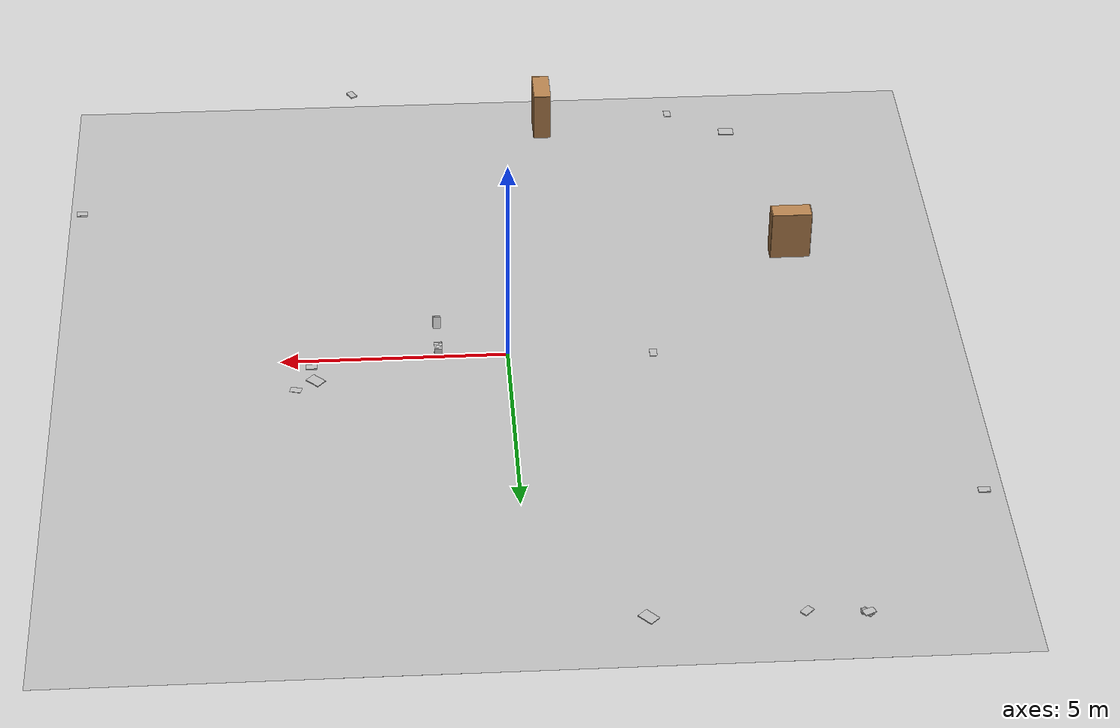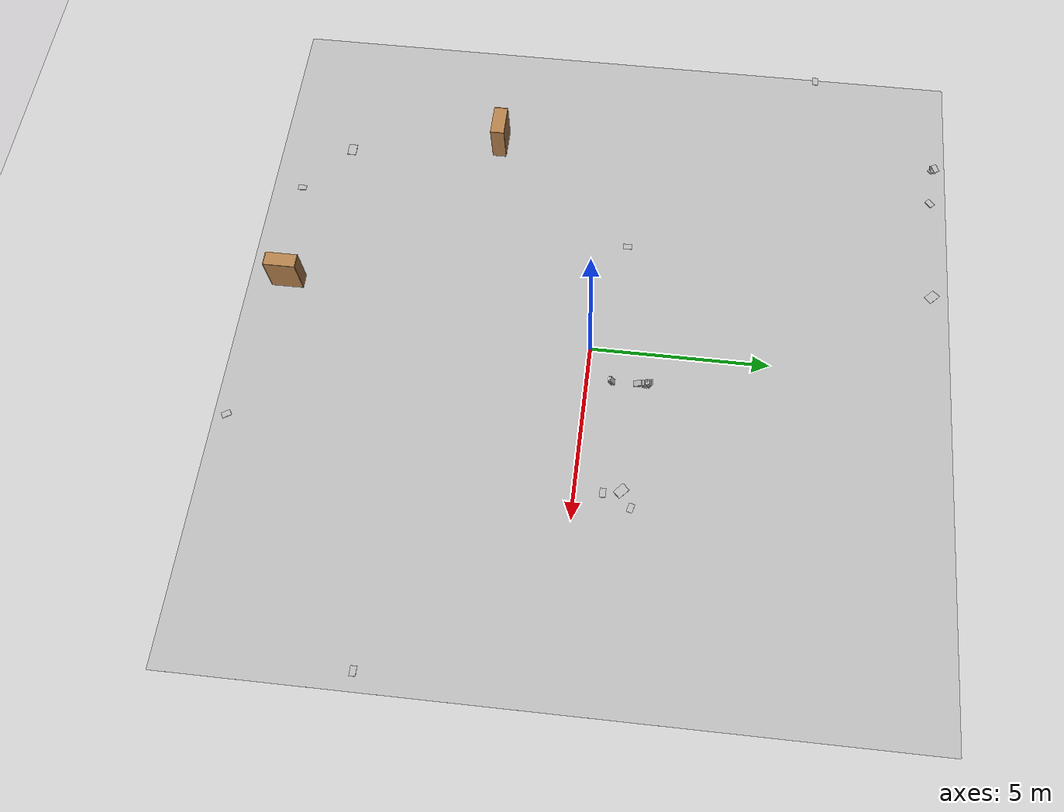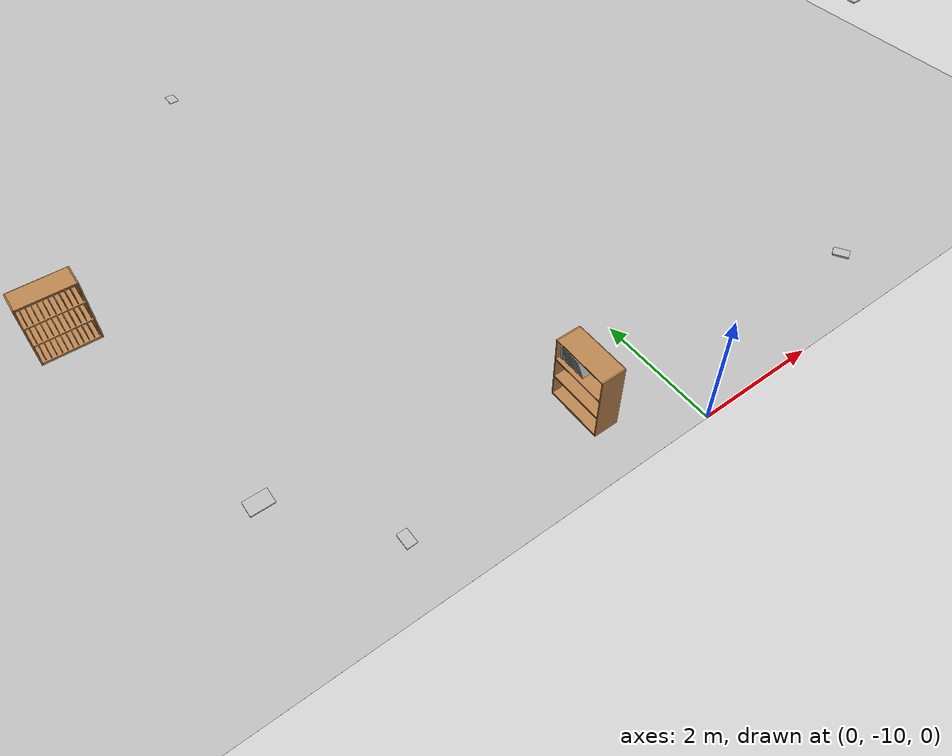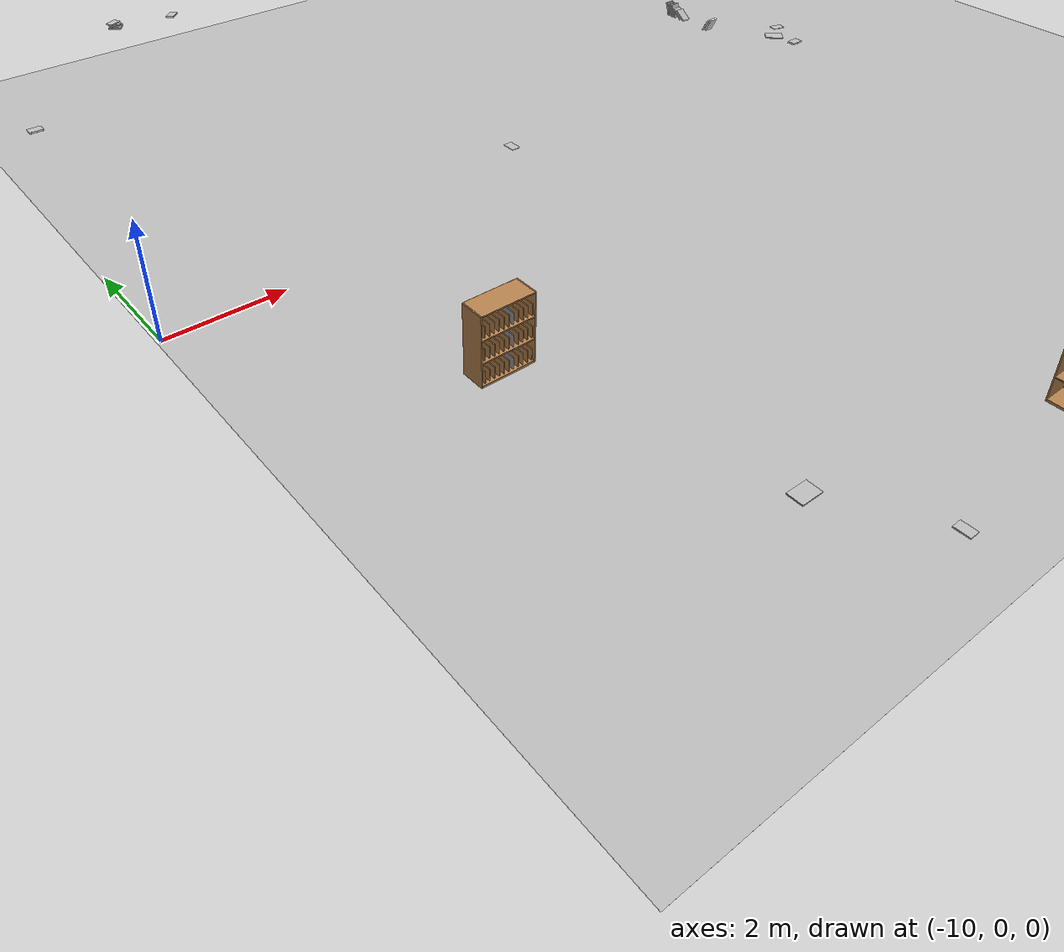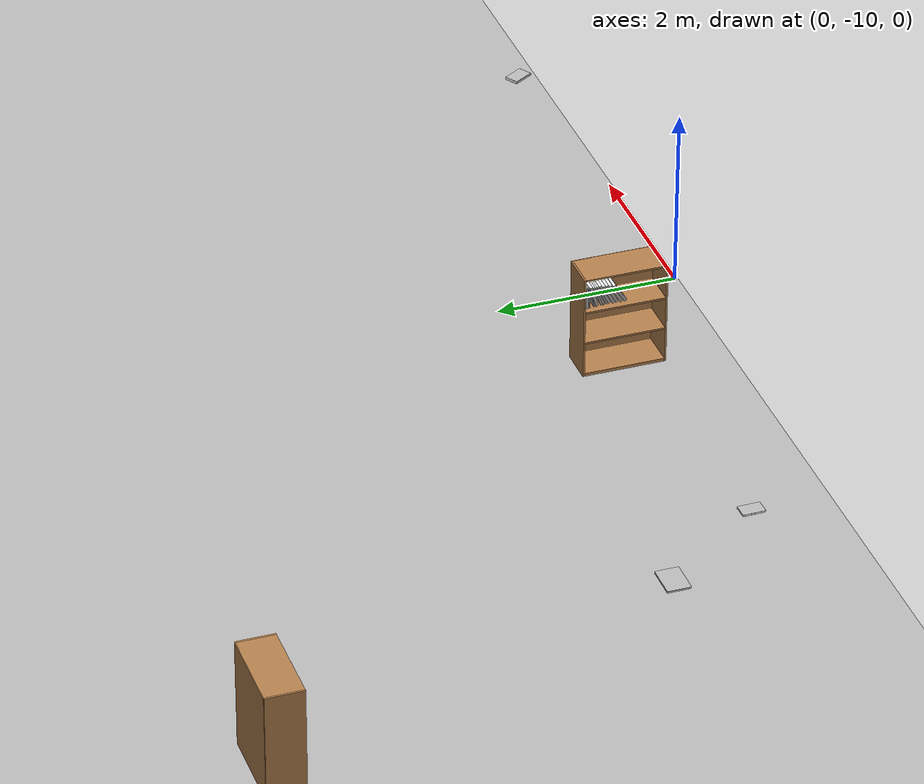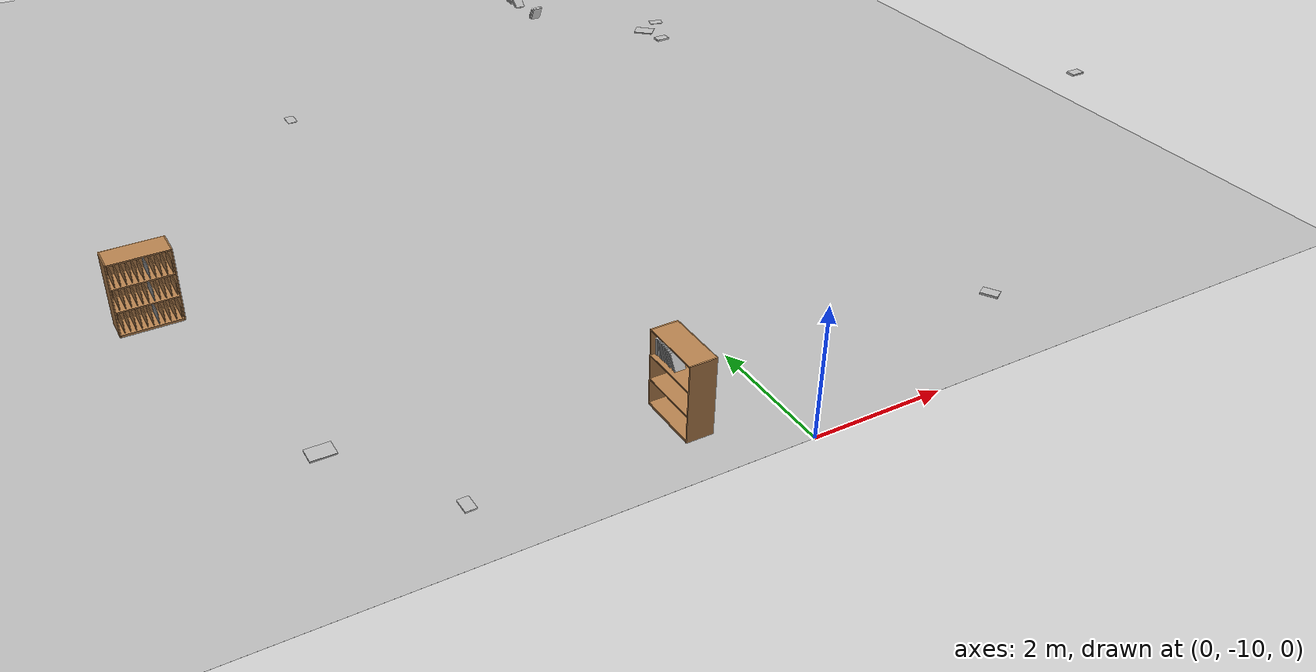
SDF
<sdf version="1.7">
 <world name="default">
  <scene><shadows>0</shadows><ambient>0.4 0.4 0.4 1</ambient><background>0.7 0.7 0.7 1</background></scene>
  <light name="sun" type="directional">
   <cast_shadows>0</cast_shadows>
   <pose>0 0 5 0 -0 0</pose>
   <diffuse>0.8 0.8 0.8 1</diffuse>
   <specular>0.1 0.1 0.1 1</specular>
   <attenuation>
    <range>1000</range>
    <constant>0.9</constant>
    <linear>0.01</linear>
    <quadratic>0.001</quadratic>
   </attenuation>
   <direction>-0.5 0.5 -1</direction>
   <spot><inner_angle>0</inner_angle><outer_angle>0</outer_angle><falloff>0</falloff></spot>
  </light>
  <physics name="default_physics" default="0" type="ode">
   <max_step_size>0.001</max_step_size>
   <real_time_factor>1</real_time_factor>
   <real_time_update_rate>1000</real_time_update_rate>
  </physics>
  <scene><ambient>0.4 0.4 0.4 1</ambient><background>0.7 0.7 0.7 1</background><shadows>1</shadows></scene>
  <spherical_coordinates>
   <surface_model>EARTH_WGS84</surface_model>
   <latitude_deg>0</latitude_deg>
   <longitude_deg>0</longitude_deg>
   <elevation>0</elevation>
   <heading_deg>0</heading_deg>
  </spherical_coordinates>
  <model name="ground_plane">
   <static>1</static>
   <link name="link">
    <collision name="collision">
     <geometry><plane><normal>0 0 1</normal><size>100 100</size></plane></geometry>
     <surface><friction><ode><mu>1</mu><mu2>1</mu2></ode></friction></surface>
    </collision>
    <visual name="visual">
     <cast_shadows>0</cast_shadows>
     <geometry><plane><normal>0 0 1</normal><size>100 100</size></plane></geometry>
     <material>
      <script><uri>file://media/materials/scripts/gazebo.material</uri><name>Gazebo/Grey</name></script>
     </material>
    </visual>
    <velocity_decay><linear>0</linear><angular>0</angular></velocity_decay>
   </link>
  </model>
  <gravity>0 0 -9.8</gravity>
  <magnetic_field>6e-06 2.3e-05 -4.2e-05</magnetic_field>
  <atmosphere type="adiabatic"/>
  <model name="bookshelf">
   <static>1</static>
   <link name="link">
    <inertial><mass>1</mass></inertial>
    <collision name="back">
     <pose>0 0.005 0.6 0 -0 0</pose>
     <geometry><box><size>0.9 0.01 1.2</size></box></geometry>
    </collision>
    <visual name="visual1">
     <pose>0 0.005 0.6 0 -0 0</pose>
     <geometry><box><size>0.9 0.01 1.2</size></box></geometry>
     <material>
      <script><uri>file://media/materials/scripts/gazebo.material</uri><name>Gazebo/Wood</name></script>
     </material>
    </visual>
    <collision name="left_side">
     <pose>0.45 -0.195 0.6 0 -0 0</pose>
     <geometry><box><size>0.02 0.4 1.2</size></box></geometry>
    </collision>
    <visual name="visual2">
     <pose>0.45 -0.195 0.6 0 -0 0</pose>
     <geometry><box><size>0.02 0.4 1.2</size></box></geometry>
     <material>
      <script><uri>file://media/materials/scripts/gazebo.material</uri><name>Gazebo/Wood</name></script>
     </material>
    </visual>
    <collision name="right_side">
     <pose>-0.45 -0.195 0.6 0 -0 0</pose>
     <geometry><box><size>0.02 0.4 1.2</size></box></geometry>
    </collision>
    <visual name="visual3">
     <pose>-0.45 -0.195 0.6 0 -0 0</pose>
     <geometry><box><size>0.02 0.4 1.2</size></box></geometry>
     <material>
      <script><uri>file://media/materials/scripts/gazebo.material</uri><name>Gazebo/Wood</name></script>
     </material>
    </visual>
    <collision name="bottom">
     <pose>0 -0.195 0.03 0 -0 0</pose>
     <geometry><box><size>0.88 0.4 0.06</size></box></geometry>
    </collision>
    <visual name="visual4">
     <pose>0 -0.195 0.03 0 -0 0</pose>
     <geometry><box><size>0.88 0.4 0.06</size></box></geometry>
     <material>
      <script><uri>file://media/materials/scripts/gazebo.material</uri><name>Gazebo/Wood</name></script>
     </material>
    </visual>
    <collision name="top">
     <pose>0 -0.195 1.19 0 -0 0</pose>
     <geometry><box><size>0.88 0.4 0.02</size></box></geometry>
    </collision>
    <visual name="visual5">
     <pose>0 -0.195 1.19 0 -0 0</pose>
     <geometry><box><size>0.88 0.4 0.02</size></box></geometry>
     <material>
      <script><uri>file://media/materials/scripts/gazebo.material</uri><name>Gazebo/Wood</name></script>
     </material>
    </visual>
    <collision name="low_shelf">
     <pose>0 -0.195 0.43 0 -0 0</pose>
     <geometry><box><size>0.88 0.4 0.02</size></box></geometry>
    </collision>
    <visual name="visual6">
     <pose>0 -0.195 0.43 0 -0 0</pose>
     <geometry><box><size>0.88 0.4 0.02</size></box></geometry>
     <material>
      <script><uri>file://media/materials/scripts/gazebo.material</uri><name>Gazebo/Wood</name></script>
     </material>
    </visual>
    <collision name="high_shelf">
     <pose>0 -0.195 0.8 0 -0 0</pose>
     <geometry><box><size>0.88 0.4 0.02</size></box></geometry>
    </collision>
    <visual name="visual7">
     <pose>0 -0.195 0.8 0 -0 0</pose>
     <geometry><box><size>0.88 0.4 0.02</size></box></geometry>
     <material>
      <script><uri>file://media/materials/scripts/gazebo.material</uri><name>Gazebo/Wood</name></script>
     </material>
    </visual>
   </link>
   <pose>-1.08243 -8.86921 0 0 0 -1.56827</pose>
  </model>
  <model name="book_10">
   <link name="cover">
    <pose>0 -0.000108 0.015405 0 -0 0</pose>
    <visual name="visual">
     <geometry><box><size>0.245 0.16 0.03</size></box></geometry>
     <material>
      <script>
       <uri>model://book_10/materials/scripts</uri>
       <uri>model://book_10/materials/textures</uri>
       <name>book_10</name>
      </script>
     </material>
    </visual>
    <collision name="collision"><geometry><box><size>0.245 0.16 0.03</size></box></geometry></collision>
   </link>
   <link name="page">
    <pose>0 0.000608 0.015405 0 -0 0</pose>
    <visual name="visual">
     <geometry><box><size>0.24502 0.15862 0.028</size></box></geometry>
     <material>
      <lighting>1</lighting>
      <ambient>1 1 1 1</ambient>
      <diffuse>1 1 1 1</diffuse>
      <specular>0.01 0.01 0.01 1</specular>
      <emissive>0 0 0 1</emissive>
      <shader type="vertex"><normal_map>__default__</normal_map></shader>
     </material>
    </visual>
    <collision name="collision"><geometry><box><size>0.245 0.16 0.03</size></box></geometry></collision>
   </link>
   <static>1</static>
   <pose>1.58252 1.72751 1.53136 -3.12764 1.25017 -1.50569</pose>
  </model>
  <model name="book_1">
   <link name="cover">
    <pose>0 -0.000108 0.015405 0 -0 0</pose>
    <visual name="visual">
     <geometry><box><size>0.245 0.16 0.03</size></box></geometry>
     <material>
      <script>
       <uri>model://book_1/materials/scripts</uri>
       <uri>model://book_1/materials/textures</uri>
       <name>book_1</name>
      </script>
     </material>
    </visual>
    <collision name="collision"><geometry><box><size>0.245 0.16 0.03</size></box></geometry></collision>
   </link>
   <link name="page">
    <pose>0 0.000608 0.015405 0 -0 0</pose>
    <visual name="visual">
     <geometry><box><size>0.24502 0.15862 0.028</size></box></geometry>
     <material>
      <lighting>1</lighting>
      <ambient>1 1 1 1</ambient>
      <diffuse>1 1 1 1</diffuse>
      <specular>0.01 0.01 0.01 1</specular>
      <emissive>0 0 0 1</emissive>
      <shader type="vertex"><normal_map>__default__</normal_map></shader>
     </material>
    </visual>
    <collision name="collision"><geometry><box><size>0.245 0.16 0.03</size></box></geometry></collision>
   </link>
   <static>1</static>
   <pose>1.57892 1.63737 1.52769 -3.11882 1.07703 -1.53154</pose>
  </model>
  <model name="book_11">
   <link name="cover">
    <pose>0 -0.000108 0.015405 0 -0 0</pose>
    <visual name="visual">
     <geometry><box><size>0.245 0.16 0.03</size></box></geometry>
     <material>
      <script>
       <uri>model://book_11/materials/scripts</uri>
       <uri>model://book_11/materials/textures</uri>
       <name>book_11</name>
      </script>
     </material>
    </visual>
    <collision name="collision"><geometry><box><size>0.245 0.16 0.03</size></box></geometry></collision>
   </link>
   <link name="page">
    <pose>0 0.000608 0.015405 0 -0 0</pose>
    <visual name="visual">
     <geometry><box><size>0.24502 0.15862 0.028</size></box></geometry>
     <material>
      <lighting>1</lighting>
      <ambient>1 1 1 1</ambient>
      <diffuse>1 1 1 1</diffuse>
      <specular>0.01 0.01 0.01 1</specular>
      <emissive>0 0 0 1</emissive>
      <shader type="vertex"><normal_map>__default__</normal_map></shader>
     </material>
    </visual>
    <collision name="collision"><geometry><box><size>0.245 0.16 0.03</size></box></geometry></collision>
   </link>
   <static>1</static>
   <pose>1.57867 1.56994 1.52807 -3.11726 1.11114 -1.52978</pose>
  </model>
  <model name="book_12">
   <link name="cover">
    <pose>0 -0.000108 0.015405 0 -0 0</pose>
    <visual name="visual">
     <geometry><box><size>0.245 0.16 0.03</size></box></geometry>
     <material>
      <script>
       <uri>model://book_12/materials/scripts</uri>
       <uri>model://book_12/materials/textures</uri>
       <name>book_12</name>
      </script>
     </material>
    </visual>
    <collision name="collision"><geometry><box><size>0.245 0.16 0.03</size></box></geometry></collision>
   </link>
   <link name="page">
    <pose>0 0.000608 0.015405 0 -0 0</pose>
    <visual name="visual">
     <geometry><box><size>0.24502 0.15862 0.028</size></box></geometry>
     <material>
      <lighting>1</lighting>
      <ambient>1 1 1 1</ambient>
      <diffuse>1 1 1 1</diffuse>
      <specular>0.01 0.01 0.01 1</specular>
      <emissive>0 0 0 1</emissive>
      <shader type="vertex"><normal_map>__default__</normal_map></shader>
     </material>
    </visual>
    <collision name="collision"><geometry><box><size>0.245 0.16 0.03</size></box></geometry></collision>
   </link>
   <static>1</static>
   <pose>1.5784 1.39365 1.50223 3.07983 0.578016 -1.63068</pose>
  </model>
  <model name="book_14">
   <link name="cover">
    <pose>0 -0.000108 0.015405 0 -0 0</pose>
    <visual name="visual">
     <geometry><box><size>0.245 0.16 0.03</size></box></geometry>
     <material>
      <script>
       <uri>model://book_14/materials/scripts</uri>
       <uri>model://book_14/materials/textures</uri>
       <name>book_14</name>
      </script>
     </material>
    </visual>
    <collision name="collision"><geometry><box><size>0.245 0.16 0.03</size></box></geometry></collision>
   </link>
   <link name="page">
    <pose>0 0.000608 0.015405 0 -0 0</pose>
    <visual name="visual">
     <geometry><box><size>0.24502 0.15862 0.028</size></box></geometry>
     <material>
      <lighting>1</lighting>
      <ambient>1 1 1 1</ambient>
      <diffuse>1 1 1 1</diffuse>
      <specular>0.01 0.01 0.01 1</specular>
      <emissive>0 0 0 1</emissive>
      <shader type="vertex"><normal_map>__default__</normal_map></shader>
     </material>
    </visual>
    <collision name="collision"><geometry><box><size>0.245 0.16 0.03</size></box></geometry></collision>
   </link>
   <static>1</static>
   <pose>1.59296 0.675656 1.51705 -0.001887 1.13528 1.58829</pose>
  </model>
  <model name="book_15">
   <link name="cover">
    <pose>0 -0.000108 0.015405 0 -0 0</pose>
    <visual name="visual">
     <geometry><box><size>0.245 0.16 0.03</size></box></geometry>
     <material>
      <script>
       <uri>model://book_15/materials/scripts</uri>
       <uri>model://book_15/materials/textures</uri>
       <name>book_15</name>
      </script>
     </material>
    </visual>
    <collision name="collision"><geometry><box><size>0.245 0.16 0.03</size></box></geometry></collision>
   </link>
   <link name="page">
    <pose>0 0.000608 0.015405 0 -0 0</pose>
    <visual name="visual">
     <geometry><box><size>0.24502 0.15862 0.028</size></box></geometry>
     <material>
      <lighting>1</lighting>
      <ambient>1 1 1 1</ambient>
      <diffuse>1 1 1 1</diffuse>
      <specular>0.01 0.01 0.01 1</specular>
      <emissive>0 0 0 1</emissive>
      <shader type="vertex"><normal_map>__default__</normal_map></shader>
     </material>
    </visual>
    <collision name="collision"><geometry><box><size>0.245 0.16 0.03</size></box></geometry></collision>
   </link>
   <static>1</static>
   <pose>1.58186 1.67602 1.52823 -3.12635 1.10761 -1.50686</pose>
  </model>
  <model name="book_16">
   <link name="cover">
    <pose>0 -0.000108 0.015405 0 -0 0</pose>
    <visual name="visual">
     <geometry><box><size>0.245 0.16 0.03</size></box></geometry>
     <material>
      <script>
       <uri>model://book_16/materials/scripts</uri>
       <uri>model://book_16/materials/textures</uri>
       <name>book_16</name>
      </script>
     </material>
    </visual>
    <collision name="collision"><geometry><box><size>0.245 0.16 0.03</size></box></geometry></collision>
   </link>
   <link name="page">
    <pose>0 0.000608 0.015405 0 -0 0</pose>
    <visual name="visual">
     <geometry><box><size>0.24502 0.15862 0.028</size></box></geometry>
     <material>
      <lighting>1</lighting>
      <ambient>1 1 1 1</ambient>
      <diffuse>1 1 1 1</diffuse>
      <specular>0.01 0.01 0.01 1</specular>
      <emissive>0 0 0 1</emissive>
      <shader type="vertex"><normal_map>__default__</normal_map></shader>
     </material>
    </visual>
    <collision name="collision"><geometry><box><size>0.245 0.16 0.03</size></box></geometry></collision>
   </link>
   <static>1</static>
   <pose>4.31939 0.767967 0.431684 0 0 -3.11812</pose>
  </model>
  <model name="book_17">
   <link name="cover">
    <pose>0 -0.000108 0.015405 0 -0 0</pose>
    <visual name="visual">
     <geometry><box><size>0.245 0.16 0.03</size></box></geometry>
     <material>
      <script>
       <uri>model://book_17/materials/scripts</uri>
       <uri>model://book_17/materials/textures</uri>
       <name>book_17</name>
      </script>
     </material>
    </visual>
    <collision name="collision"><geometry><box><size>0.245 0.16 0.03</size></box></geometry></collision>
   </link>
   <link name="page">
    <pose>0 0.000608 0.015405 0 -0 0</pose>
    <visual name="visual">
     <geometry><box><size>0.24502 0.15862 0.028</size></box></geometry>
     <material>
      <lighting>1</lighting>
      <ambient>1 1 1 1</ambient>
      <diffuse>1 1 1 1</diffuse>
      <specular>0.01 0.01 0.01 1</specular>
      <emissive>0 0 0 1</emissive>
      <shader type="vertex"><normal_map>__default__</normal_map></shader>
     </material>
    </visual>
    <collision name="collision"><geometry><box><size>0.245 0.16 0.03</size></box></geometry></collision>
   </link>
   <static>1</static>
   <pose>1.58009 1.60475 1.53124 3.06968 1.07706 -1.63479</pose>
  </model>
  <model name="book_18">
   <link name="cover">
    <pose>0 -0.000108 0.015405 0 -0 0</pose>
    <visual name="visual">
     <geometry><box><size>0.245 0.16 0.03</size></box></geometry>
     <material>
      <script>
       <uri>model://book_18/materials/scripts</uri>
       <uri>model://book_18/materials/textures</uri>
       <name>book_18</name>
      </script>
     </material>
    </visual>
    <collision name="collision"><geometry><box><size>0.245 0.16 0.03</size></box></geometry></collision>
   </link>
   <link name="page">
    <pose>0 0.000608 0.015405 0 -0 0</pose>
    <visual name="visual">
     <geometry><box><size>0.24502 0.15862 0.028</size></box></geometry>
     <material>
      <lighting>1</lighting>
      <ambient>1 1 1 1</ambient>
      <diffuse>1 1 1 1</diffuse>
      <specular>0.01 0.01 0.01 1</specular>
      <emissive>0 0 0 1</emissive>
      <shader type="vertex"><normal_map>__default__</normal_map></shader>
     </material>
    </visual>
    <collision name="collision"><geometry><box><size>0.245 0.16 0.03</size></box></geometry></collision>
   </link>
   <static>1</static>
   <pose>1.5794 0.721517 1.51174 -0.022284 1.06499 1.55051</pose>
  </model>
  <model name="book_2">
   <link name="cover">
    <pose>0 -0.000108 0.015405 0 -0 0</pose>
    <visual name="visual">
     <geometry><box><size>0.245 0.16 0.03</size></box></geometry>
     <material>
      <script>
       <uri>model://book_2/materials/scripts</uri>
       <uri>model://book_2/materials/textures</uri>
       <name>book_2</name>
      </script>
     </material>
    </visual>
    <collision name="collision"><geometry><box><size>0.245 0.16 0.03</size></box></geometry></collision>
   </link>
   <link name="page">
    <pose>0 0.000608 0.015405 0 -0 0</pose>
    <visual name="visual">
     <geometry><box><size>0.24502 0.15862 0.028</size></box></geometry>
     <material>
      <lighting>1</lighting>
      <ambient>1 1 1 1</ambient>
      <diffuse>1 1 1 1</diffuse>
      <specular>0.01 0.01 0.01 1</specular>
      <emissive>0 0 0 1</emissive>
      <shader type="vertex"><normal_map>__default__</normal_map></shader>
     </material>
    </visual>
    <collision name="collision"><geometry><box><size>0.245 0.16 0.03</size></box></geometry></collision>
   </link>
   <static>1</static>
   <pose>1.58038 1.4756 1.50855 -3.12301 0.677539 -1.55887</pose>
  </model>
  <model name="book_20">
   <link name="cover">
    <pose>0 -0.000108 0.015405 0 -0 0</pose>
    <visual name="visual">
     <geometry><box><size>0.245 0.16 0.03</size></box></geometry>
     <material>
      <script>
       <uri>model://book_20/materials/scripts</uri>
       <uri>model://book_20/materials/textures</uri>
       <name>book_20</name>
      </script>
     </material>
    </visual>
    <collision name="collision"><geometry><box><size>0.245 0.16 0.03</size></box></geometry></collision>
   </link>
   <link name="page">
    <pose>0 0.000608 0.015405 0 -0 0</pose>
    <visual name="visual">
     <geometry><box><size>0.24502 0.15862 0.028</size></box></geometry>
     <material>
      <lighting>1</lighting>
      <ambient>1 1 1 1</ambient>
      <diffuse>1 1 1 1</diffuse>
      <specular>0.01 0.01 0.01 1</specular>
      <emissive>0 0 0 1</emissive>
      <shader type="vertex"><normal_map>__default__</normal_map></shader>
     </material>
    </visual>
    <collision name="collision"><geometry><box><size>0.245 0.16 0.03</size></box></geometry></collision>
   </link>
   <static>1</static>
   <pose>-1.33514 -8.47354 0.933303 -3.1415 -1.50452 1.64295</pose>
  </model>
  <model name="book_21">
   <link name="cover">
    <pose>0 -0.000108 0.005 0 -0 0</pose>
    <visual name="visual">
     <geometry><box><size>0.245 0.16 0.01</size></box></geometry>
     <material>
      <script>
       <uri>model://book_21/materials/scripts</uri>
       <uri>model://book_21/materials/textures</uri>
       <name>book_21</name>
      </script>
     </material>
    </visual>
    <collision name="collision"><geometry><box><size>0.245 0.16 0.01</size></box></geometry></collision>
   </link>
   <link name="page">
    <pose>0 0.000608 0.005 0 -0 0</pose>
    <visual name="visual">
     <geometry><box><size>0.24502 0.15862 0.008</size></box></geometry>
     <material>
      <lighting>1</lighting>
      <ambient>1 1 1 1</ambient>
      <diffuse>1 1 1 1</diffuse>
      <specular>0.01 0.01 0.01 1</specular>
      <emissive>0 0 0 1</emissive>
      <shader type="vertex"><normal_map>__default__</normal_map></shader>
     </material>
    </visual>
    <collision name="collision"><geometry><box><size>0.245 0.16 0.008</size></box></geometry></collision>
   </link>
   <static>1</static>
   <pose>-1.32998 -8.52484 0.933 -3.13832 -1.32475 1.56842</pose>
  </model>
  <model name="book_3">
   <link name="cover">
    <pose>0 -0.000108 0.01 0 -0 0</pose>
    <visual name="visual">
     <geometry><box><size>0.245 0.16 0.02</size></box></geometry>
     <material>
      <script>
       <uri>model://book_3/materials/scripts</uri>
       <uri>model://book_3/materials/textures</uri>
       <name>book_3</name>
      </script>
     </material>
    </visual>
    <collision name="collision"><geometry><box><size>0.245 0.16 0.02</size></box></geometry></collision>
   </link>
   <link name="page">
    <pose>0 0.000608 0.01 0 -0 0</pose>
    <visual name="visual">
     <geometry><box><size>0.24502 0.15862 0.018</size></box></geometry>
     <material>
      <lighting>1</lighting>
      <ambient>1 1 1 1</ambient>
      <diffuse>1 1 1 1</diffuse>
      <specular>0.01 0.01 0.01 1</specular>
      <emissive>0 0 0 1</emissive>
      <shader type="vertex"><normal_map>__default__</normal_map></shader>
     </material>
    </visual>
    <collision name="collision"><geometry><box><size>0.245 0.16 0.018</size></box></geometry></collision>
   </link>
   <static>1</static>
   <pose>-1.34027 -8.59409 0.94392 -3.1394 -1.1994 1.56955</pose>
  </model>
  <model name="book_4">
   <link name="cover">
    <pose>0 -0.000108 0.01 0 -0 0</pose>
    <visual name="visual">
     <geometry><box><size>0.245 0.16 0.02</size></box></geometry>
     <material>
      <script>
       <uri>model://book_4/materials/scripts</uri>
       <uri>model://book_4/materials/textures</uri>
       <name>book_4</name>
      </script>
     </material>
     <cast_shadows>0</cast_shadows>
    </visual>
    <collision name="collision"><geometry><box><size>0.245 0.16 0.02</size></box></geometry></collision>
   </link>
   <link name="page">
    <pose>0 0.000608 0.01 0 -0 0</pose>
    <visual name="visual">
     <geometry><box><size>0.24502 0.15862 0.018</size></box></geometry>
     <material>
      <lighting>1</lighting>
      <ambient>1 1 1 1</ambient>
      <diffuse>1 1 1 1</diffuse>
      <specular>0.01 0.01 0.01 1</specular>
      <emissive>0 0 0 1</emissive>
      <shader type="vertex"><normal_map>__default__</normal_map></shader>
     </material>
     <cast_shadows>0</cast_shadows>
    </visual>
    <collision name="collision"><geometry><box><size>0.245 0.16 0.018</size></box></geometry></collision>
   </link>
   <static>1</static>
   <pose>-1.33002 -8.62073 0.934243 -3.13946 -1.18764 1.56962</pose>
  </model>
  <model name="book_9">
   <link name="cover">
    <pose>0 -0.000108 0.005 0 -0 0</pose>
    <visual name="visual">
     <geometry><box><size>0.245 0.16 0.01</size></box></geometry>
     <material>
      <script>
       <uri>model://book_9/materials/scripts</uri>
       <uri>model://book_9/materials/textures</uri>
       <name>book_9</name>
      </script>
     </material>
    </visual>
    <collision name="collision"><geometry><box><size>0.245 0.16 0.01</size></box></geometry></collision>
   </link>
   <link name="page">
    <pose>0 0.000608 0.005 0 -0 0</pose>
    <visual name="visual">
     <geometry><box><size>0.24502 0.15862 0.008</size></box></geometry>
     <material>
      <lighting>1</lighting>
      <ambient>1 1 1 1</ambient>
      <diffuse>1 1 1 1</diffuse>
      <specular>0.01 0.01 0.01 1</specular>
      <emissive>0 0 0 1</emissive>
      <shader type="vertex"><normal_map>__default__</normal_map></shader>
     </material>
    </visual>
    <collision name="collision"><geometry><box><size>0.245 0.16 0.008</size></box></geometry></collision>
   </link>
   <static>1</static>
   <pose>-1.32998 -8.49338 0.933 -3.13349 -1.47234 1.57155</pose>
  </model>
  <model name="book_16_0">
   <link name="cover">
    <pose>0 -0.000108 0.015405 0 -0 0</pose>
    <visual name="visual">
     <geometry><box><size>0.245 0.16 0.03</size></box></geometry>
     <material>
      <script>
       <uri>model://book_16/materials/scripts</uri>
       <uri>model://book_16/materials/textures</uri>
       <name>book_16</name>
      </script>
     </material>
    </visual>
    <collision name="collision"><geometry><box><size>0.245 0.16 0.03</size></box></geometry></collision>
   </link>
   <link name="page">
    <pose>0 0.000608 0.015405 0 -0 0</pose>
    <visual name="visual">
     <geometry><box><size>0.24502 0.15862 0.028</size></box></geometry>
     <material>
      <lighting>1</lighting>
      <ambient>1 1 1 1</ambient>
      <diffuse>1 1 1 1</diffuse>
      <specular>0.01 0.01 0.01 1</specular>
      <emissive>0 0 0 1</emissive>
      <shader type="vertex"><normal_map>__default__</normal_map></shader>
     </material>
    </visual>
    <collision name="collision"><geometry><box><size>0.245 0.16 0.03</size></box></geometry></collision>
   </link>
   <static>1</static>
   <pose>-1.32786 -8.56422 0.936359 -3.13881 -1.28012 1.56893</pose>
  </model>
  <model name="book_13">
   <link name="cover">
    <pose>0 -0.000108 0.015405 0 -0 0</pose>
    <visual name="visual">
     <geometry><box><size>0.245 0.16 0.03</size></box></geometry>
     <material>
      <script>
       <uri>model://book_13/materials/scripts</uri>
       <uri>model://book_13/materials/textures</uri>
       <name>book_13</name>
      </script>
     </material>
    </visual>
    <collision name="collision"><geometry><box><size>0.245 0.16 0.03</size></box></geometry></collision>
   </link>
   <link name="page">
    <pose>0 0.000608 0.015405 0 -0 0</pose>
    <visual name="visual">
     <geometry><box><size>0.24502 0.15862 0.028</size></box></geometry>
     <material>
      <lighting>1</lighting>
      <ambient>1 1 1 1</ambient>
      <diffuse>1 1 1 1</diffuse>
      <specular>0.01 0.01 0.01 1</specular>
      <emissive>0 0 0 1</emissive>
      <shader type="vertex"><normal_map>__default__</normal_map></shader>
     </material>
    </visual>
    <collision name="collision"><geometry><box><size>0.245 0.16 0.03</size></box></geometry></collision>
   </link>
   <static>1</static>
   <pose>-1.33006 -8.72144 0.935666 -3.13982 -1.10393 1.57001</pose>
  </model>
  <model name="book_12_0">
   <link name="cover">
    <pose>0 -0.000108 0.015405 0 -0 0</pose>
    <visual name="visual">
     <geometry><box><size>0.245 0.16 0.03</size></box></geometry>
     <material>
      <script>
       <uri>model://book_12/materials/scripts</uri>
       <uri>model://book_12/materials/textures</uri>
       <name>book_12</name>
      </script>
     </material>
    </visual>
    <collision name="collision"><geometry><box><size>0.245 0.16 0.03</size></box></geometry></collision>
   </link>
   <link name="page">
    <pose>0 0.000608 0.015405 0 -0 0</pose>
    <visual name="visual">
     <geometry><box><size>0.24502 0.15862 0.028</size></box></geometry>
     <material>
      <lighting>1</lighting>
      <ambient>1 1 1 1</ambient>
      <diffuse>1 1 1 1</diffuse>
      <specular>0.01 0.01 0.01 1</specular>
      <emissive>0 0 0 1</emissive>
      <shader type="vertex"><normal_map>__default__</normal_map></shader>
     </material>
    </visual>
    <collision name="collision"><geometry><box><size>0.245 0.16 0.03</size></box></geometry></collision>
   </link>
   <static>1</static>
   <pose>-1.33007 -8.75802 0.937574 -3.13986 -1.0924 1.57006</pose>
  </model>
  <model name="book_6">
   <link name="cover">
    <pose>0 -0.000108 0.01 0 -0 0</pose>
    <visual name="visual">
     <geometry><box><size>0.245 0.16 0.02</size></box></geometry>
     <material>
      <script>
       <uri>model://book_6/materials/scripts</uri>
       <uri>model://book_6/materials/textures</uri>
       <name>book_6</name>
      </script>
     </material>
    </visual>
    <collision name="collision"><geometry><box><size>0.245 0.16 0.02</size></box></geometry></collision>
   </link>
   <link name="page">
    <pose>0 0.000608 0.01 0 -0 0</pose>
    <visual name="visual">
     <geometry><box><size>0.24502 0.15862 0.018</size></box></geometry>
     <material>
      <lighting>1</lighting>
      <ambient>1 1 1 1</ambient>
      <diffuse>1 1 1 1</diffuse>
      <specular>0.01 0.01 0.01 1</specular>
      <emissive>0 0 0 1</emissive>
      <shader type="vertex"><normal_map>__default__</normal_map></shader>
     </material>
    </visual>
    <collision name="collision"><geometry><box><size>0.245 0.16 0.018</size></box></geometry></collision>
   </link>
   <static>1</static>
   <pose>-1.33004 -8.64658 0.937038 -3.13966 -1.14492 1.56984</pose>
  </model>
  <model name="book_8">
   <link name="cover">
    <pose>0 -0.000108 0.005 0 -0 0</pose>
    <visual name="visual">
     <geometry><box><size>0.245 0.16 0.01</size></box></geometry>
     <material>
      <script>
       <uri>model://book_8/materials/scripts</uri>
       <uri>model://book_8/materials/textures</uri>
       <name>book_8</name>
      </script>
     </material>
    </visual>
    <collision name="collision"><geometry><box><size>0.245 0.16 0.01</size></box></geometry></collision>
   </link>
   <link name="page">
    <pose>0 0.000608 0.005 0 -0 0</pose>
    <visual name="visual">
     <geometry><box><size>0.24502 0.15862 0.008</size></box></geometry>
     <material>
      <lighting>1</lighting>
      <ambient>1 1 1 1</ambient>
      <diffuse>1 1 1 1</diffuse>
      <specular>0.01 0.01 0.01 1</specular>
      <emissive>0 0 0 1</emissive>
      <shader type="vertex"><normal_map>__default__</normal_map></shader>
     </material>
    </visual>
    <collision name="collision"><geometry><box><size>0.245 0.16 0.008</size></box></geometry></collision>
   </link>
   <static>1</static>
   <pose>4.65089 1.52824 0.431029 0 -0 2.87142</pose>
  </model>
  <model name="book_19">
   <link name="cover">
    <pose>0 -0.000108 0.015405 0 -0 0</pose>
    <visual name="visual">
     <geometry><box><size>0.245 0.16 0.03</size></box></geometry>
     <material>
      <script>
       <uri>model://book_19/materials/scripts</uri>
       <uri>model://book_19/materials/textures</uri>
       <name>book_19</name>
      </script>
     </material>
    </visual>
    <collision name="collision"><geometry><box><size>0.245 0.16 0.03</size></box></geometry></collision>
   </link>
   <link name="page">
    <pose>0 0.000608 0.015405 0 -0 0</pose>
    <visual name="visual">
     <geometry><box><size>0.24502 0.15862 0.028</size></box></geometry>
     <material>
      <lighting>1</lighting>
      <ambient>1 1 1 1</ambient>
      <diffuse>1 1 1 1</diffuse>
      <specular>0.01 0.01 0.01 1</specular>
      <emissive>0 0 0 1</emissive>
      <shader type="vertex"><normal_map>__default__</normal_map></shader>
     </material>
    </visual>
    <collision name="collision"><geometry><box><size>0.245 0.16 0.03</size></box></geometry></collision>
   </link>
   <static>1</static>
   <pose>-1.32315 -8.68246 0.939077 -3.13968 -1.14225 1.56985</pose>
  </model>
  <model name="book_13_0">
   <link name="cover">
    <pose>0 -0.000108 0.015405 0 -0 0</pose>
    <visual name="visual">
     <geometry><box><size>0.245 0.16 0.03</size></box></geometry>
     <material>
      <script>
       <uri>model://book_13/materials/scripts</uri>
       <uri>model://book_13/materials/textures</uri>
       <name>book_13</name>
      </script>
     </material>
    </visual>
    <collision name="collision"><geometry><box><size>0.245 0.16 0.03</size></box></geometry></collision>
   </link>
   <link name="page">
    <pose>0 0.000608 0.015405 0 -0 0</pose>
    <visual name="visual">
     <geometry><box><size>0.24502 0.15862 0.028</size></box></geometry>
     <material>
      <lighting>1</lighting>
      <ambient>1 1 1 1</ambient>
      <diffuse>1 1 1 1</diffuse>
      <specular>0.01 0.01 0.01 1</specular>
      <emissive>0 0 0 1</emissive>
      <shader type="vertex"><normal_map>__default__</normal_map></shader>
     </material>
    </visual>
    <collision name="collision"><geometry><box><size>0.245 0.16 0.03</size></box></geometry></collision>
   </link>
   <static>1</static>
   <pose>-1.33008 -8.84522 0.930105 -3.14009 -1.01364 1.57031</pose>
  </model>
  <model name="book_14_0">
   <link name="cover">
    <pose>0 -0.000108 0.015405 0 -0 0</pose>
    <visual name="visual">
     <geometry><box><size>0.245 0.16 0.03</size></box></geometry>
     <material>
      <script>
       <uri>model://book_14/materials/scripts</uri>
       <uri>model://book_14/materials/textures</uri>
       <name>book_14</name>
      </script>
     </material>
    </visual>
    <collision name="collision"><geometry><box><size>0.245 0.16 0.03</size></box></geometry></collision>
   </link>
   <link name="page">
    <pose>0 0.000608 0.015405 0 -0 0</pose>
    <visual name="visual">
     <geometry><box><size>0.24502 0.15862 0.028</size></box></geometry>
     <material>
      <lighting>1</lighting>
      <ambient>1 1 1 1</ambient>
      <diffuse>1 1 1 1</diffuse>
      <specular>0.01 0.01 0.01 1</specular>
      <emissive>0 0 0 1</emissive>
      <shader type="vertex"><normal_map>__default__</normal_map></shader>
     </material>
    </visual>
    <collision name="collision"><geometry><box><size>0.245 0.16 0.03</size></box></geometry></collision>
   </link>
   <static>1</static>
   <pose>-1.33007 -8.8029 0.931916 -3.14002 -1.04019 1.57024</pose>
  </model>
  <model name="newspaper_1">
   <link name="link_0">
    <visual name="visual">
     <geometry><box><size>0.35 0.25 0.02</size></box></geometry>
     <material>
      <script>
       <uri>model://newspaper_1/materials/scripts</uri>
       <uri>model://newspaper_1/materials/textures</uri>
       <name>newspaper_1</name>
      </script>
     </material>
    </visual>
    <collision name="collision"><geometry><box><size>0.35 0.25 0.02</size></box></geometry></collision>
   </link>
   <static>1</static>
   <pose>-5.65633 -7.79435 0.455927 0 -0 0</pose>
  </model>
  <model name="book_6_0">
   <link name="cover">
    <pose>0 -0.000108 0.01 0 -0 0</pose>
    <visual name="visual">
     <geometry><box><size>0.245 0.16 0.02</size></box></geometry>
     <material>
      <script>
       <uri>model://book_6/materials/scripts</uri>
       <uri>model://book_6/materials/textures</uri>
       <name>book_6</name>
      </script>
     </material>
    </visual>
    <collision name="collision"><geometry><box><size>0.245 0.16 0.02</size></box></geometry></collision>
   </link>
   <link name="page">
    <pose>0 0.000608 0.01 0 -0 0</pose>
    <visual name="visual">
     <geometry><box><size>0.24502 0.15862 0.018</size></box></geometry>
     <material>
      <lighting>1</lighting>
      <ambient>1 1 1 1</ambient>
      <diffuse>1 1 1 1</diffuse>
      <specular>0.01 0.01 0.01 1</specular>
      <emissive>0 0 0 1</emissive>
      <shader type="vertex"><normal_map>__default__</normal_map></shader>
     </material>
    </visual>
    <collision name="collision"><geometry><box><size>0.245 0.16 0.018</size></box></geometry></collision>
   </link>
   <static>1</static>
   <pose>-4.37689 -9.12673 0.113948 0 -0 1.58993</pose>
  </model>
  <model name="book_9_0">
   <link name="cover">
    <pose>0 -0.000108 0.005 0 -0 0</pose>
    <visual name="visual">
     <geometry><box><size>0.245 0.16 0.01</size></box></geometry>
     <material>
      <script>
       <uri>model://book_9/materials/scripts</uri>
       <uri>model://book_9/materials/textures</uri>
       <name>book_9</name>
      </script>
     </material>
    </visual>
    <collision name="collision"><geometry><box><size>0.245 0.16 0.01</size></box></geometry></collision>
   </link>
   <link name="page">
    <pose>0 0.000608 0.005 0 -0 0</pose>
    <visual name="visual">
     <geometry><box><size>0.24502 0.15862 0.008</size></box></geometry>
     <material>
      <lighting>1</lighting>
      <ambient>1 1 1 1</ambient>
      <diffuse>1 1 1 1</diffuse>
      <specular>0.01 0.01 0.01 1</specular>
      <emissive>0 0 0 1</emissive>
      <shader type="vertex"><normal_map>__default__</normal_map></shader>
     </material>
    </visual>
    <collision name="collision"><geometry><box><size>0.245 0.16 0.008</size></box></geometry></collision>
   </link>
   <static>1</static>
   <pose>-3.1266 0.731411 0.499788 0 -0 1.5743</pose>
  </model>
  <model name="book_18_0">
   <link name="cover">
    <pose>0 -0.000108 0.015405 0 -0 0</pose>
    <visual name="visual">
     <geometry><box><size>0.245 0.16 0.03</size></box></geometry>
     <material>
      <script>
       <uri>model://book_18/materials/scripts</uri>
       <uri>model://book_18/materials/textures</uri>
       <name>book_18</name>
      </script>
     </material>
    </visual>
    <collision name="collision"><geometry><box><size>0.245 0.16 0.03</size></box></geometry></collision>
   </link>
   <link name="page">
    <pose>0 0.000608 0.015405 0 -0 0</pose>
    <visual name="visual">
     <geometry><box><size>0.24502 0.15862 0.028</size></box></geometry>
     <material>
      <lighting>1</lighting>
      <ambient>1 1 1 1</ambient>
      <diffuse>1 1 1 1</diffuse>
      <specular>0.01 0.01 0.01 1</specular>
      <emissive>0 0 0 1</emissive>
      <shader type="vertex"><normal_map>__default__</normal_map></shader>
     </material>
    </visual>
    <collision name="collision"><geometry><box><size>0.245 0.16 0.03</size></box></geometry></collision>
   </link>
   <static>1</static>
   <pose>3.29779 -9.39066 0.764084 0 0 -1.01851</pose>
  </model>
  <model name="book_14_1">
   <link name="cover">
    <pose>0 -0.000108 0.015405 0 -0 0</pose>
    <visual name="visual">
     <geometry><box><size>0.245 0.16 0.03</size></box></geometry>
     <material>
      <script>
       <uri>model://book_14/materials/scripts</uri>
       <uri>model://book_14/materials/textures</uri>
       <name>book_14</name>
      </script>
     </material>
    </visual>
    <collision name="collision"><geometry><box><size>0.245 0.16 0.03</size></box></geometry></collision>
   </link>
   <link name="page">
    <pose>0 0.000608 0.015405 0 -0 0</pose>
    <visual name="visual">
     <geometry><box><size>0.24502 0.15862 0.028</size></box></geometry>
     <material>
      <lighting>1</lighting>
      <ambient>1 1 1 1</ambient>
      <diffuse>1 1 1 1</diffuse>
      <specular>0.01 0.01 0.01 1</specular>
      <emissive>0 0 0 1</emissive>
      <shader type="vertex"><normal_map>__default__</normal_map></shader>
     </material>
    </visual>
    <collision name="collision"><geometry><box><size>0.245 0.16 0.03</size></box></geometry></collision>
   </link>
   <static>1</static>
   <pose>9.54563 -4.75392 0.763218 0 -0 0</pose>
  </model>
  <model name="newspaper_3">
   <link name="link_0">
    <visual name="visual">
     <geometry><box><size>0.35 0.25 0.02</size></box></geometry>
     <material>
      <script>
       <uri>model://newspaper_3/materials/scripts</uri>
       <uri>model://newspaper_3/materials/textures</uri>
       <name>newspaper_3</name>
      </script>
     </material>
    </visual>
    <collision name="collision"><geometry><box><size>0.35 0.25 0.02</size></box></geometry></collision>
   </link>
   <static>1</static>
   <pose>4.22036 1.24525 0.44562 0 0 -0.747151</pose>
  </model>
  <model name="newspaper_1_0">
   <link name="link_0">
    <visual name="visual">
     <geometry><box><size>0.35 0.25 0.02</size></box></geometry>
     <material>
      <script>
       <uri>model://newspaper_1/materials/scripts</uri>
       <uri>model://newspaper_1/materials/textures</uri>
       <name>newspaper_1</name>
      </script>
     </material>
    </visual>
    <collision name="collision"><geometry><box><size>0.35 0.25 0.02</size></box></geometry></collision>
   </link>
   <static>1</static>
   <pose>-2.24932 9.33811 0.733586 0 0 -0.805858</pose>
  </model>
  <model name="book_20_0">
   <link name="cover">
    <pose>0 -0.000108 0.015405 0 -0 0</pose>
    <visual name="visual">
     <geometry><box><size>0.245 0.16 0.03</size></box></geometry>
     <material>
      <script>
       <uri>model://book_20/materials/scripts</uri>
       <uri>model://book_20/materials/textures</uri>
       <name>book_20</name>
      </script>
     </material>
    </visual>
    <collision name="collision"><geometry><box><size>0.245 0.16 0.03</size></box></geometry></collision>
   </link>
   <link name="page">
    <pose>0 0.000608 0.015405 0 -0 0</pose>
    <visual name="visual">
     <geometry><box><size>0.24502 0.15862 0.028</size></box></geometry>
     <material>
      <lighting>1</lighting>
      <ambient>1 1 1 1</ambient>
      <diffuse>1 1 1 1</diffuse>
      <specular>0.01 0.01 0.01 1</specular>
      <emissive>0 0 0 1</emissive>
      <shader type="vertex"><normal_map>__default__</normal_map></shader>
     </material>
    </visual>
    <collision name="collision"><geometry><box><size>0.245 0.16 0.03</size></box></geometry></collision>
   </link>
   <static>1</static>
   <pose>-6.53491 9.43104 0.722202 0 0 -0.67887</pose>
  </model>
  <model name="book_14_2">
   <link name="cover">
    <pose>0 -0.000108 0.015405 0 -0 0</pose>
    <visual name="visual">
     <geometry><box><size>0.245 0.16 0.03</size></box></geometry>
     <material>
      <script>
       <uri>model://book_14/materials/scripts</uri>
       <uri>model://book_14/materials/textures</uri>
       <name>book_14</name>
      </script>
     </material>
    </visual>
    <collision name="collision"><geometry><box><size>0.245 0.16 0.03</size></box></geometry></collision>
   </link>
   <link name="page">
    <pose>0 0.000608 0.015405 0 -0 0</pose>
    <visual name="visual">
     <geometry><box><size>0.24502 0.15862 0.028</size></box></geometry>
     <material>
      <lighting>1</lighting>
      <ambient>1 1 1 1</ambient>
      <diffuse>1 1 1 1</diffuse>
      <specular>0.01 0.01 0.01 1</specular>
      <emissive>0 0 0 1</emissive>
      <shader type="vertex"><normal_map>__default__</normal_map></shader>
     </material>
    </visual>
    <collision name="collision"><geometry><box><size>0.245 0.16 0.03</size></box></geometry></collision>
   </link>
   <static>1</static>
   <pose>-6.5246 9.44373 0.75565 0 -0 0</pose>
  </model>
  <model name="book_7">
   <link name="cover">
    <pose>0 -0.000108 0.005 0 -0 0</pose>
    <visual name="visual">
     <geometry><box><size>0.245 0.16 0.01</size></box></geometry>
     <material>
      <script>
       <uri>model://book_7/materials/scripts</uri>
       <uri>model://book_7/materials/textures</uri>
       <name>book_7</name>
      </script>
     </material>
    </visual>
    <collision name="collision"><geometry><box><size>0.245 0.16 0.01</size></box></geometry></collision>
   </link>
   <link name="page">
    <pose>0 0.000608 0.005 0 -0 0</pose>
    <visual name="visual">
     <geometry><box><size>0.24502 0.15862 0.008</size></box></geometry>
     <material>
      <lighting>1</lighting>
      <ambient>1 1 1 1</ambient>
      <diffuse>1 1 1 1</diffuse>
      <specular>0.01 0.01 0.01 1</specular>
      <emissive>0 0 0 1</emissive>
      <shader type="vertex"><normal_map>__default__</normal_map></shader>
     </material>
    </visual>
    <collision name="collision"><geometry><box><size>0.245 0.16 0.008</size></box></geometry></collision>
   </link>
   <static>1</static>
   <pose>-6.53983 9.47094 0.790989 0 0 -0.119957</pose>
  </model>
  <model name="book_4_0">
   <link name="cover">
    <pose>0 -0.000108 0.01 0 -0 0</pose>
    <visual name="visual">
     <geometry><box><size>0.245 0.16 0.02</size></box></geometry>
     <material>
      <script>
       <uri>model://book_4/materials/scripts</uri>
       <uri>model://book_4/materials/textures</uri>
       <name>book_4</name>
      </script>
     </material>
     <cast_shadows>0</cast_shadows>
    </visual>
    <collision name="collision"><geometry><box><size>0.245 0.16 0.02</size></box></geometry></collision>
   </link>
   <link name="page">
    <pose>0 0.000608 0.01 0 -0 0</pose>
    <visual name="visual">
     <geometry><box><size>0.24502 0.15862 0.018</size></box></geometry>
     <material>
      <lighting>1</lighting>
      <ambient>1 1 1 1</ambient>
      <diffuse>1 1 1 1</diffuse>
      <specular>0.01 0.01 0.01 1</specular>
      <emissive>0 0 0 1</emissive>
      <shader type="vertex"><normal_map>__default__</normal_map></shader>
     </material>
     <cast_shadows>0</cast_shadows>
    </visual>
    <collision name="collision"><geometry><box><size>0.245 0.16 0.018</size></box></geometry></collision>
   </link>
   <static>1</static>
   <pose>-6.54776 9.49752 0.802886 0 -0 0.398229</pose>
  </model>
  <model name="book_1_0">
   <link name="cover">
    <pose>0 -0.000108 0.015405 0 -0 0</pose>
    <visual name="visual">
     <geometry><box><size>0.245 0.16 0.03</size></box></geometry>
     <material>
      <script>
       <uri>model://book_1/materials/scripts</uri>
       <uri>model://book_1/materials/textures</uri>
       <name>book_1</name>
      </script>
     </material>
    </visual>
    <collision name="collision"><geometry><box><size>0.245 0.16 0.03</size></box></geometry></collision>
   </link>
   <link name="page">
    <pose>0 0.000608 0.015405 0 -0 0</pose>
    <visual name="visual">
     <geometry><box><size>0.24502 0.15862 0.028</size></box></geometry>
     <material>
      <lighting>1</lighting>
      <ambient>1 1 1 1</ambient>
      <diffuse>1 1 1 1</diffuse>
      <specular>0.01 0.01 0.01 1</specular>
      <emissive>0 0 0 1</emissive>
      <shader type="vertex"><normal_map>__default__</normal_map></shader>
     </material>
    </visual>
    <collision name="collision"><geometry><box><size>0.245 0.16 0.03</size></box></geometry></collision>
   </link>
   <static>1</static>
   <pose>-5.35464 9.33771 0.723979 0 -0 0.76417</pose>
  </model>
  <model name="book_10_0">
   <link name="cover">
    <pose>0 -0.000108 0.015405 0 -0 0</pose>
    <visual name="visual">
     <geometry><box><size>0.245 0.16 0.03</size></box></geometry>
     <material>
      <script>
       <uri>model://book_10/materials/scripts</uri>
       <uri>model://book_10/materials/textures</uri>
       <name>book_10</name>
      </script>
     </material>
    </visual>
    <collision name="collision"><geometry><box><size>0.245 0.16 0.03</size></box></geometry></collision>
   </link>
   <link name="page">
    <pose>0 0.000608 0.015405 0 -0 0</pose>
    <visual name="visual">
     <geometry><box><size>0.24502 0.15862 0.028</size></box></geometry>
     <material>
      <lighting>1</lighting>
      <ambient>1 1 1 1</ambient>
      <diffuse>1 1 1 1</diffuse>
      <specular>0.01 0.01 0.01 1</specular>
      <emissive>0 0 0 1</emissive>
      <shader type="vertex"><normal_map>__default__</normal_map></shader>
     </material>
    </visual>
    <collision name="collision"><geometry><box><size>0.245 0.16 0.03</size></box></geometry></collision>
   </link>
   <static>1</static>
   <pose>-9.45293 5.92846 0.722801 0 -0 3.12799</pose>
  </model>
  <model name="Floor_room">
   <link name="main">
    <pose>0 0 0.01 0 -0 0</pose>
    <collision name="main_Collision"><geometry><box><size>20 20 0.001</size></box></geometry></collision>
    <visual name="main_Visual">
     <geometry><box><size>20 20 0.001</size></box></geometry>
     <material>
      <script>
       <uri>model://Floor_room/materials/scripts</uri>
       <uri>model://Floor_room/materials/textures</uri>
       <name>floor_room</name>
      </script>
     </material>
    </visual>
   </link>
   <static>1</static>
   <pose>-0.0718 -0.016894 0.012233 0 -0 0</pose>
  </model>
  <model name="bookshelf_0">
   <link name="link">
    <inertial><mass>1</mass></inertial>
    <visual name="visual1">
     <pose>0 0.005 0.6 0 -0 0</pose>
     <geometry><box><size>0.9 0.01 1.2</size></box></geometry>
     <material>
      <script><uri>file://media/materials/scripts/gazebo.material</uri><name>Gazebo/Wood</name></script>
      <shader type="pixel"/>
     </material>
    </visual>
    <visual name="visual7">
     <pose>0 -0.195 0.8 0 -0 0</pose>
     <geometry><box><size>0.88 0.4 0.02</size></box></geometry>
     <material>
      <script><uri>file://media/materials/scripts/gazebo.material</uri><name>Gazebo/Wood</name></script>
      <shader type="pixel"/>
     </material>
    </visual>
    <visual name="visual5">
     <pose>0 -0.195 1.19 0 -0 0</pose>
     <geometry><box><size>0.88 0.4 0.02</size></box></geometry>
     <material>
      <script><uri>file://media/materials/scripts/gazebo.material</uri><name>Gazebo/Wood</name></script>
      <shader type="pixel"/>
     </material>
    </visual>
    <visual name="visual6">
     <pose>0 -0.195 0.43 0 -0 0</pose>
     <geometry><box><size>0.88 0.4 0.02</size></box></geometry>
     <material>
      <script><uri>file://media/materials/scripts/gazebo.material</uri><name>Gazebo/Wood</name></script>
      <shader type="pixel"/>
     </material>
    </visual>
    <visual name="visual3">
     <pose>-0.45 -0.195 0.6 0 -0 0</pose>
     <geometry><box><size>0.02 0.4 1.2</size></box></geometry>
     <material>
      <script><uri>file://media/materials/scripts/gazebo.material</uri><name>Gazebo/Wood</name></script>
      <shader type="pixel"/>
     </material>
    </visual>
    <visual name="visual2">
     <pose>0.45 -0.195 0.6 0 -0 0</pose>
     <geometry><box><size>0.02 0.4 1.2</size></box></geometry>
     <material>
      <script><uri>file://media/materials/scripts/gazebo.material</uri><name>Gazebo/Wood</name></script>
      <shader type="pixel"/>
     </material>
    </visual>
    <visual name="visual4">
     <pose>0 -0.195 0.03 0 -0 0</pose>
     <geometry><box><size>0.88 0.4 0.06</size></box></geometry>
     <material>
      <script><uri>file://media/materials/scripts/gazebo.material</uri><name>Gazebo/Wood</name></script>
      <shader type="pixel"/>
     </material>
    </visual>
    <collision name="back">
     <pose>0 0.005 0.6 0 -0 0</pose>
     <geometry><box><size>0.9 0.01 1.2</size></box></geometry>
     <surface>
      <friction>
       <ode><mu>1</mu><mu2>1</mu2><fdir1>0 0 0</fdir1><slip1>0</slip1><slip2>0</slip2></ode>
       <torsional>
        <coefficient>1</coefficient>
        <patch_radius>0</patch_radius>
        <surface_radius>0</surface_radius>
        <use_patch_radius>1</use_patch_radius>
        <ode><slip>0</slip></ode>
       </torsional>
      </friction>
      <bounce><restitution_coefficient>0</restitution_coefficient><threshold>1e+06</threshold></bounce>
      <contact>
       <collide_without_contact>0</collide_without_contact>
       <collide_without_contact_bitmask>1</collide_without_contact_bitmask>
       <collide_bitmask>1</collide_bitmask>
       <ode>
        <soft_cfm>0</soft_cfm>
        <soft_erp>0.2</soft_erp>
        <kp>1e+13</kp>
        <kd>1</kd>
        <max_vel>0.01</max_vel>
        <min_depth>0</min_depth>
       </ode>
       <bullet>
        <split_impulse>1</split_impulse>
        <split_impulse_penetration_threshold>-0.01</split_impulse_penetration_threshold>
        <soft_cfm>0</soft_cfm>
        <soft_erp>0.2</soft_erp>
        <kp>1e+13</kp>
        <kd>1</kd>
       </bullet>
      </contact>
     </surface>
    </collision>
    <collision name="right_side">
     <pose>-0.45 -0.195 0.6 0 -0 0</pose>
     <geometry><box><size>0.02 0.4 1.2</size></box></geometry>
     <surface>
      <friction>
       <ode><mu>1</mu><mu2>1</mu2><fdir1>0 0 0</fdir1><slip1>0</slip1><slip2>0</slip2></ode>
       <torsional>
        <coefficient>1</coefficient>
        <patch_radius>0</patch_radius>
        <surface_radius>0</surface_radius>
        <use_patch_radius>1</use_patch_radius>
        <ode><slip>0</slip></ode>
       </torsional>
      </friction>
      <bounce><restitution_coefficient>0</restitution_coefficient><threshold>1e+06</threshold></bounce>
      <contact>
       <collide_without_contact>0</collide_without_contact>
       <collide_without_contact_bitmask>1</collide_without_contact_bitmask>
       <collide_bitmask>1</collide_bitmask>
       <ode>
        <soft_cfm>0</soft_cfm>
        <soft_erp>0.2</soft_erp>
        <kp>1e+13</kp>
        <kd>1</kd>
        <max_vel>0.01</max_vel>
        <min_depth>0</min_depth>
       </ode>
       <bullet>
        <split_impulse>1</split_impulse>
        <split_impulse_penetration_threshold>-0.01</split_impulse_penetration_threshold>
        <soft_cfm>0</soft_cfm>
        <soft_erp>0.2</soft_erp>
        <kp>1e+13</kp>
        <kd>1</kd>
       </bullet>
      </contact>
     </surface>
    </collision>
    <collision name="left_side">
     <pose>0.45 -0.195 0.6 0 -0 0</pose>
     <geometry><box><size>0.02 0.4 1.2</size></box></geometry>
     <surface>
      <friction>
       <ode><mu>1</mu><mu2>1</mu2><fdir1>0 0 0</fdir1><slip1>0</slip1><slip2>0</slip2></ode>
       <torsional>
        <coefficient>1</coefficient>
        <patch_radius>0</patch_radius>
        <surface_radius>0</surface_radius>
        <use_patch_radius>1</use_patch_radius>
        <ode><slip>0</slip></ode>
       </torsional>
      </friction>
      <bounce><restitution_coefficient>0</restitution_coefficient><threshold>1e+06</threshold></bounce>
      <contact>
       <collide_without_contact>0</collide_without_contact>
       <collide_without_contact_bitmask>1</collide_without_contact_bitmask>
       <collide_bitmask>1</collide_bitmask>
       <ode>
        <soft_cfm>0</soft_cfm>
        <soft_erp>0.2</soft_erp>
        <kp>1e+13</kp>
        <kd>1</kd>
        <max_vel>0.01</max_vel>
        <min_depth>0</min_depth>
       </ode>
       <bullet>
        <split_impulse>1</split_impulse>
        <split_impulse_penetration_threshold>-0.01</split_impulse_penetration_threshold>
        <soft_cfm>0</soft_cfm>
        <soft_erp>0.2</soft_erp>
        <kp>1e+13</kp>
        <kd>1</kd>
       </bullet>
      </contact>
     </surface>
    </collision>
    <collision name="high_shelf">
     <pose>0 -0.195 0.8 0 -0 0</pose>
     <geometry><box><size>0.88 0.4 0.02</size></box></geometry>
     <surface>
      <friction>
       <ode><mu>1</mu><mu2>1</mu2><fdir1>0 0 0</fdir1><slip1>0</slip1><slip2>0</slip2></ode>
       <torsional>
        <coefficient>1</coefficient>
        <patch_radius>0</patch_radius>
        <surface_radius>0</surface_radius>
        <use_patch_radius>1</use_patch_radius>
        <ode><slip>0</slip></ode>
       </torsional>
      </friction>
      <bounce><restitution_coefficient>0</restitution_coefficient><threshold>1e+06</threshold></bounce>
      <contact>
       <collide_without_contact>0</collide_without_contact>
       <collide_without_contact_bitmask>1</collide_without_contact_bitmask>
       <collide_bitmask>1</collide_bitmask>
       <ode>
        <soft_cfm>0</soft_cfm>
        <soft_erp>0.2</soft_erp>
        <kp>1e+13</kp>
        <kd>1</kd>
        <max_vel>0.01</max_vel>
        <min_depth>0</min_depth>
       </ode>
       <bullet>
        <split_impulse>1</split_impulse>
        <split_impulse_penetration_threshold>-0.01</split_impulse_penetration_threshold>
        <soft_cfm>0</soft_cfm>
        <soft_erp>0.2</soft_erp>
        <kp>1e+13</kp>
        <kd>1</kd>
       </bullet>
      </contact>
     </surface>
    </collision>
    <collision name="bottom">
     <pose>0 -0.195 0.03 0 -0 0</pose>
     <geometry><box><size>0.88 0.4 0.06</size></box></geometry>
     <surface>
      <friction>
       <ode><mu>1</mu><mu2>1</mu2><fdir1>0 0 0</fdir1><slip1>0</slip1><slip2>0</slip2></ode>
       <torsional>
        <coefficient>1</coefficient>
        <patch_radius>0</patch_radius>
        <surface_radius>0</surface_radius>
        <use_patch_radius>1</use_patch_radius>
        <ode><slip>0</slip></ode>
       </torsional>
      </friction>
      <bounce><restitution_coefficient>0</restitution_coefficient><threshold>1e+06</threshold></bounce>
      <contact>
       <collide_without_contact>0</collide_without_contact>
       <collide_without_contact_bitmask>1</collide_without_contact_bitmask>
       <collide_bitmask>1</collide_bitmask>
       <ode>
        <soft_cfm>0</soft_cfm>
        <soft_erp>0.2</soft_erp>
        <kp>1e+13</kp>
        <kd>1</kd>
        <max_vel>0.01</max_vel>
        <min_depth>0</min_depth>
       </ode>
       <bullet>
        <split_impulse>1</split_impulse>
        <split_impulse_penetration_threshold>-0.01</split_impulse_penetration_threshold>
        <soft_cfm>0</soft_cfm>
        <soft_erp>0.2</soft_erp>
        <kp>1e+13</kp>
        <kd>1</kd>
       </bullet>
      </contact>
     </surface>
    </collision>
    <collision name="top">
     <pose>0 -0.195 1.19 0 -0 0</pose>
     <geometry><box><size>0.88 0.4 0.02</size></box></geometry>
     <surface>
      <friction>
       <ode><mu>1</mu><mu2>1</mu2><fdir1>0 0 0</fdir1><slip1>0</slip1><slip2>0</slip2></ode>
       <torsional>
        <coefficient>1</coefficient>
        <patch_radius>0</patch_radius>
        <surface_radius>0</surface_radius>
        <use_patch_radius>1</use_patch_radius>
        <ode><slip>0</slip></ode>
       </torsional>
      </friction>
      <bounce><restitution_coefficient>0</restitution_coefficient><threshold>1e+06</threshold></bounce>
      <contact>
       <collide_without_contact>0</collide_without_contact>
       <collide_without_contact_bitmask>1</collide_without_contact_bitmask>
       <collide_bitmask>1</collide_bitmask>
       <ode>
        <soft_cfm>0</soft_cfm>
        <soft_erp>0.2</soft_erp>
        <kp>1e+13</kp>
        <kd>1</kd>
        <max_vel>0.01</max_vel>
        <min_depth>0</min_depth>
       </ode>
       <bullet>
        <split_impulse>1</split_impulse>
        <split_impulse_penetration_threshold>-0.01</split_impulse_penetration_threshold>
        <soft_cfm>0</soft_cfm>
        <soft_erp>0.2</soft_erp>
        <kp>1e+13</kp>
        <kd>1</kd>
       </bullet>
      </contact>
     </surface>
    </collision>
    <collision name="low_shelf">
     <pose>0 -0.195 0.43 0 -0 0</pose>
     <geometry><box><size>0.88 0.4 0.02</size></box></geometry>
     <surface>
      <friction>
       <ode><mu>1</mu><mu2>1</mu2><fdir1>0 0 0</fdir1><slip1>0</slip1><slip2>0</slip2></ode>
       <torsional>
        <coefficient>1</coefficient>
        <patch_radius>0</patch_radius>
        <surface_radius>0</surface_radius>
        <use_patch_radius>1</use_patch_radius>
        <ode><slip>0</slip></ode>
       </torsional>
      </friction>
      <bounce><restitution_coefficient>0</restitution_coefficient><threshold>1e+06</threshold></bounce>
      <contact>
       <collide_without_contact>0</collide_without_contact>
       <collide_without_contact_bitmask>1</collide_without_contact_bitmask>
       <collide_bitmask>1</collide_bitmask>
       <ode>
        <soft_cfm>0</soft_cfm>
        <soft_erp>0.2</soft_erp>
        <kp>1e+13</kp>
        <kd>1</kd>
        <max_vel>0.01</max_vel>
        <min_depth>0</min_depth>
       </ode>
       <bullet>
        <split_impulse>1</split_impulse>
        <split_impulse_penetration_threshold>-0.01</split_impulse_penetration_threshold>
        <soft_cfm>0</soft_cfm>
        <soft_erp>0.2</soft_erp>
        <kp>1e+13</kp>
        <kd>1</kd>
       </bullet>
      </contact>
     </surface>
    </collision>
   </link>
   <link name="link_1">
    <inertial>
     <mass>1</mass>
     <inertia>
      <ixx>0.166667</ixx>
      <ixy>0</ixy>
      <ixz>0</ixz>
      <iyy>0.166667</iyy>
      <iyz>0</iyz>
      <izz>0.166667</izz>
     </inertia>
    </inertial>
    <pose>-0.38 -0.195 0.907998 0 0 -1.57</pose>
    <visual name="visual">
     <geometry><box><size>0.35 0.01 0.2</size></box></geometry>
     <material>
      <script><uri>file://media/materials/scripts/gazebo.material</uri><name>Gazebo/Wood</name></script>
      <shader type="pixel"/>
     </material>
    </visual>
    <visual name="ModelPreview_3::link_1::visual_1">
     <geometry><box><size>0.35 0.01 0.2</size></box></geometry>
     <material>
      <lighting>1</lighting>
      <script><uri>file://media/materials/scripts/gazebo.material</uri><name>Gazebo/Grey</name></script>
      <shader type="pixel"><normal_map>__default__</normal_map></shader>
      <ambient>0.3 0.3 0.3 1</ambient>
      <diffuse>0.7 0.7 0.7 1</diffuse>
      <specular>0.01 0.01 0.01 1</specular>
      <emissive>0 0 0 1</emissive>
     </material>
    </visual>
    <collision name="collision">
     <geometry><box><size>0.35 0.01 0.2</size></box></geometry>
     <surface>
      <friction>
       <ode><mu>1</mu><mu2>1</mu2><fdir1>0 0 0</fdir1><slip1>0</slip1><slip2>0</slip2></ode>
       <torsional>
        <coefficient>1</coefficient>
        <patch_radius>0</patch_radius>
        <surface_radius>0</surface_radius>
        <use_patch_radius>1</use_patch_radius>
        <ode><slip>0</slip></ode>
       </torsional>
      </friction>
      <bounce><restitution_coefficient>0</restitution_coefficient><threshold>1e+06</threshold></bounce>
      <contact>
       <collide_without_contact>0</collide_without_contact>
       <collide_without_contact_bitmask>1</collide_without_contact_bitmask>
       <collide_bitmask>1</collide_bitmask>
       <ode>
        <soft_cfm>0</soft_cfm>
        <soft_erp>0.2</soft_erp>
        <kp>1e+13</kp>
        <kd>1</kd>
        <max_vel>0.01</max_vel>
        <min_depth>0</min_depth>
       </ode>
       <bullet>
        <split_impulse>1</split_impulse>
        <split_impulse_penetration_threshold>-0.01</split_impulse_penetration_threshold>
        <soft_cfm>0</soft_cfm>
        <soft_erp>0.2</soft_erp>
        <kp>1e+13</kp>
        <kd>1</kd>
       </bullet>
      </contact>
     </surface>
    </collision>
   </link>
   <link name="link_2">
    <inertial>
     <mass>1</mass>
     <inertia>
      <ixx>0.166667</ixx>
      <ixy>0</ixy>
      <ixz>0</ixz>
      <iyy>0.166667</iyy>
      <iyz>0</iyz>
      <izz>0.166667</izz>
     </inertia>
    </inertial>
    <pose>-0.3 -0.195 0.907998 0 0 -1.57</pose>
    <visual name="visual">
     <geometry><box><size>0.35 0.01 0.2</size></box></geometry>
     <material>
      <script><uri>file://media/materials/scripts/gazebo.material</uri><name>Gazebo/Wood</name></script>
      <shader type="pixel"/>
     </material>
    </visual>
    <visual name="ModelPreview_3::link_1::visual_1">
     <geometry><box><size>0.35 0.01 0.2</size></box></geometry>
     <material>
      <lighting>1</lighting>
      <script><uri>file://media/materials/scripts/gazebo.material</uri><name>Gazebo/Grey</name></script>
      <shader type="pixel"><normal_map>__default__</normal_map></shader>
      <ambient>0.3 0.3 0.3 1</ambient>
      <diffuse>0.7 0.7 0.7 1</diffuse>
      <specular>0.01 0.01 0.01 1</specular>
      <emissive>0 0 0 1</emissive>
     </material>
    </visual>
    <collision name="collision">
     <geometry><box><size>0.35 0.01 0.2</size></box></geometry>
     <surface>
      <friction>
       <ode><mu>1</mu><mu2>1</mu2><fdir1>0 0 0</fdir1><slip1>0</slip1><slip2>0</slip2></ode>
       <torsional>
        <coefficient>1</coefficient>
        <patch_radius>0</patch_radius>
        <surface_radius>0</surface_radius>
        <use_patch_radius>1</use_patch_radius>
        <ode><slip>0</slip></ode>
       </torsional>
      </friction>
      <bounce><restitution_coefficient>0</restitution_coefficient><threshold>1e+06</threshold></bounce>
      <contact>
       <collide_without_contact>0</collide_without_contact>
       <collide_without_contact_bitmask>1</collide_without_contact_bitmask>
       <collide_bitmask>1</collide_bitmask>
       <ode>
        <soft_cfm>0</soft_cfm>
        <soft_erp>0.2</soft_erp>
        <kp>1e+13</kp>
        <kd>1</kd>
        <max_vel>0.01</max_vel>
        <min_depth>0</min_depth>
       </ode>
       <bullet>
        <split_impulse>1</split_impulse>
        <split_impulse_penetration_threshold>-0.01</split_impulse_penetration_threshold>
        <soft_cfm>0</soft_cfm>
        <soft_erp>0.2</soft_erp>
        <kp>1e+13</kp>
        <kd>1</kd>
       </bullet>
      </contact>
     </surface>
    </collision>
   </link>
   <link name="link_3">
    <inertial>
     <mass>1</mass>
     <inertia>
      <ixx>0.166667</ixx>
      <ixy>0</ixy>
      <ixz>0</ixz>
      <iyy>0.166667</iyy>
      <iyz>0</iyz>
      <izz>0.166667</izz>
     </inertia>
    </inertial>
    <pose>-0.22 -0.195 0.907998 0 0 -1.57</pose>
    <visual name="visual">
     <geometry><box><size>0.35 0.01 0.2</size></box></geometry>
     <material>
      <script><uri>file://media/materials/scripts/gazebo.material</uri><name>Gazebo/Wood</name></script>
      <shader type="pixel"/>
     </material>
    </visual>
    <visual name="ModelPreview_3::link_1::visual_1">
     <geometry><box><size>0.35 0.01 0.2</size></box></geometry>
     <material>
      <lighting>1</lighting>
      <script><uri>file://media/materials/scripts/gazebo.material</uri><name>Gazebo/Grey</name></script>
      <shader type="pixel"><normal_map>__default__</normal_map></shader>
      <ambient>0.3 0.3 0.3 1</ambient>
      <diffuse>0.7 0.7 0.7 1</diffuse>
      <specular>0.01 0.01 0.01 1</specular>
      <emissive>0 0 0 1</emissive>
     </material>
    </visual>
    <collision name="collision">
     <geometry><box><size>0.35 0.01 0.2</size></box></geometry>
     <surface>
      <friction>
       <ode><mu>1</mu><mu2>1</mu2><fdir1>0 0 0</fdir1><slip1>0</slip1><slip2>0</slip2></ode>
       <torsional>
        <coefficient>1</coefficient>
        <patch_radius>0</patch_radius>
        <surface_radius>0</surface_radius>
        <use_patch_radius>1</use_patch_radius>
        <ode><slip>0</slip></ode>
       </torsional>
      </friction>
      <bounce><restitution_coefficient>0</restitution_coefficient><threshold>1e+06</threshold></bounce>
      <contact>
       <collide_without_contact>0</collide_without_contact>
       <collide_without_contact_bitmask>1</collide_without_contact_bitmask>
       <collide_bitmask>1</collide_bitmask>
       <ode>
        <soft_cfm>0</soft_cfm>
        <soft_erp>0.2</soft_erp>
        <kp>1e+13</kp>
        <kd>1</kd>
        <max_vel>0.01</max_vel>
        <min_depth>0</min_depth>
       </ode>
       <bullet>
        <split_impulse>1</split_impulse>
        <split_impulse_penetration_threshold>-0.01</split_impulse_penetration_threshold>
        <soft_cfm>0</soft_cfm>
        <soft_erp>0.2</soft_erp>
        <kp>1e+13</kp>
        <kd>1</kd>
       </bullet>
      </contact>
     </surface>
    </collision>
   </link>
   <link name="link_4">
    <inertial>
     <mass>1</mass>
     <inertia>
      <ixx>0.166667</ixx>
      <ixy>0</ixy>
      <ixz>0</ixz>
      <iyy>0.166667</iyy>
      <iyz>0</iyz>
      <izz>0.166667</izz>
     </inertia>
    </inertial>
    <pose>-0.14 -0.195 0.907998 0 0 -1.57</pose>
    <visual name="visual">
     <geometry><box><size>0.35 0.01 0.2</size></box></geometry>
     <material>
      <script><uri>file://media/materials/scripts/gazebo.material</uri><name>Gazebo/Wood</name></script>
      <shader type="pixel"/>
     </material>
    </visual>
    <visual name="ModelPreview_3::link_1::visual_1">
     <geometry><box><size>0.35 0.01 0.2</size></box></geometry>
     <material>
      <lighting>1</lighting>
      <script><uri>file://media/materials/scripts/gazebo.material</uri><name>Gazebo/Grey</name></script>
      <shader type="pixel"><normal_map>__default__</normal_map></shader>
      <ambient>0.3 0.3 0.3 1</ambient>
      <diffuse>0.7 0.7 0.7 1</diffuse>
      <specular>0.01 0.01 0.01 1</specular>
      <emissive>0 0 0 1</emissive>
     </material>
    </visual>
    <collision name="collision">
     <geometry><box><size>0.35 0.01 0.2</size></box></geometry>
     <surface>
      <friction>
       <ode><mu>1</mu><mu2>1</mu2><fdir1>0 0 0</fdir1><slip1>0</slip1><slip2>0</slip2></ode>
       <torsional>
        <coefficient>1</coefficient>
        <patch_radius>0</patch_radius>
        <surface_radius>0</surface_radius>
        <use_patch_radius>1</use_patch_radius>
        <ode><slip>0</slip></ode>
       </torsional>
      </friction>
      <bounce><restitution_coefficient>0</restitution_coefficient><threshold>1e+06</threshold></bounce>
      <contact>
       <collide_without_contact>0</collide_without_contact>
       <collide_without_contact_bitmask>1</collide_without_contact_bitmask>
       <collide_bitmask>1</collide_bitmask>
       <ode>
        <soft_cfm>0</soft_cfm>
        <soft_erp>0.2</soft_erp>
        <kp>1e+13</kp>
        <kd>1</kd>
        <max_vel>0.01</max_vel>
        <min_depth>0</min_depth>
       </ode>
       <bullet>
        <split_impulse>1</split_impulse>
        <split_impulse_penetration_threshold>-0.01</split_impulse_penetration_threshold>
        <soft_cfm>0</soft_cfm>
        <soft_erp>0.2</soft_erp>
        <kp>1e+13</kp>
        <kd>1</kd>
       </bullet>
      </contact>
     </surface>
    </collision>
   </link>
   <link name="link_5">
    <inertial>
     <mass>1</mass>
     <inertia>
      <ixx>0.166667</ixx>
      <ixy>0</ixy>
      <ixz>0</ixz>
      <iyy>0.166667</iyy>
      <iyz>0</iyz>
      <izz>0.166667</izz>
     </inertia>
    </inertial>
    <pose>-0.06 -0.195 0.907998 0 0 -1.57</pose>
    <visual name="visual">
     <geometry><box><size>0.35 0.01 0.2</size></box></geometry>
     <material>
      <script><uri>file://media/materials/scripts/gazebo.material</uri><name>Gazebo/Wood</name></script>
      <shader type="pixel"/>
     </material>
    </visual>
    <visual name="ModelPreview_3::link_1::visual_1">
     <geometry><box><size>0.35 0.01 0.2</size></box></geometry>
     <material>
      <lighting>1</lighting>
      <script><uri>file://media/materials/scripts/gazebo.material</uri><name>Gazebo/Grey</name></script>
      <shader type="pixel"><normal_map>__default__</normal_map></shader>
      <ambient>0.3 0.3 0.3 1</ambient>
      <diffuse>0.7 0.7 0.7 1</diffuse>
      <specular>0.01 0.01 0.01 1</specular>
      <emissive>0 0 0 1</emissive>
     </material>
    </visual>
    <collision name="collision">
     <geometry><box><size>0.35 0.01 0.2</size></box></geometry>
     <surface>
      <friction>
       <ode><mu>1</mu><mu2>1</mu2><fdir1>0 0 0</fdir1><slip1>0</slip1><slip2>0</slip2></ode>
       <torsional>
        <coefficient>1</coefficient>
        <patch_radius>0</patch_radius>
        <surface_radius>0</surface_radius>
        <use_patch_radius>1</use_patch_radius>
        <ode><slip>0</slip></ode>
       </torsional>
      </friction>
      <bounce><restitution_coefficient>0</restitution_coefficient><threshold>1e+06</threshold></bounce>
      <contact>
       <collide_without_contact>0</collide_without_contact>
       <collide_without_contact_bitmask>1</collide_without_contact_bitmask>
       <collide_bitmask>1</collide_bitmask>
       <ode>
        <soft_cfm>0</soft_cfm>
        <soft_erp>0.2</soft_erp>
        <kp>1e+13</kp>
        <kd>1</kd>
        <max_vel>0.01</max_vel>
        <min_depth>0</min_depth>
       </ode>
       <bullet>
        <split_impulse>1</split_impulse>
        <split_impulse_penetration_threshold>-0.01</split_impulse_penetration_threshold>
        <soft_cfm>0</soft_cfm>
        <soft_erp>0.2</soft_erp>
        <kp>1e+13</kp>
        <kd>1</kd>
       </bullet>
      </contact>
     </surface>
    </collision>
   </link>
   <link name="link_6">
    <inertial>
     <mass>1</mass>
     <inertia>
      <ixx>0.166667</ixx>
      <ixy>0</ixy>
      <ixz>0</ixz>
      <iyy>0.166667</iyy>
      <iyz>0</iyz>
      <izz>0.166667</izz>
     </inertia>
    </inertial>
    <pose>0.02 -0.195 0.907998 0 0 -1.57</pose>
    <visual name="visual">
     <geometry><box><size>0.35 0.01 0.2</size></box></geometry>
     <material>
      <script><uri>file://media/materials/scripts/gazebo.material</uri><name>Gazebo/Wood</name></script>
      <shader type="pixel"/>
     </material>
    </visual>
    <visual name="ModelPreview_3::link_1::visual_1">
     <geometry><box><size>0.35 0.01 0.2</size></box></geometry>
     <material>
      <lighting>1</lighting>
      <script><uri>file://media/materials/scripts/gazebo.material</uri><name>Gazebo/Grey</name></script>
      <shader type="pixel"><normal_map>__default__</normal_map></shader>
      <ambient>0.3 0.3 0.3 1</ambient>
      <diffuse>0.7 0.7 0.7 1</diffuse>
      <specular>0.01 0.01 0.01 1</specular>
      <emissive>0 0 0 1</emissive>
     </material>
    </visual>
    <collision name="collision">
     <geometry><box><size>0.35 0.01 0.2</size></box></geometry>
     <surface>
      <friction>
       <ode><mu>1</mu><mu2>1</mu2><fdir1>0 0 0</fdir1><slip1>0</slip1><slip2>0</slip2></ode>
       <torsional>
        <coefficient>1</coefficient>
        <patch_radius>0</patch_radius>
        <surface_radius>0</surface_radius>
        <use_patch_radius>1</use_patch_radius>
        <ode><slip>0</slip></ode>
       </torsional>
      </friction>
      <bounce><restitution_coefficient>0</restitution_coefficient><threshold>1e+06</threshold></bounce>
      <contact>
       <collide_without_contact>0</collide_without_contact>
       <collide_without_contact_bitmask>1</collide_without_contact_bitmask>
       <collide_bitmask>1</collide_bitmask>
       <ode>
        <soft_cfm>0</soft_cfm>
        <soft_erp>0.2</soft_erp>
        <kp>1e+13</kp>
        <kd>1</kd>
        <max_vel>0.01</max_vel>
        <min_depth>0</min_depth>
       </ode>
       <bullet>
        <split_impulse>1</split_impulse>
        <split_impulse_penetration_threshold>-0.01</split_impulse_penetration_threshold>
        <soft_cfm>0</soft_cfm>
        <soft_erp>0.2</soft_erp>
        <kp>1e+13</kp>
        <kd>1</kd>
       </bullet>
      </contact>
     </surface>
    </collision>
   </link>
   <link name="link_7">
    <inertial>
     <mass>1</mass>
     <inertia>
      <ixx>0.166667</ixx>
      <ixy>0</ixy>
      <ixz>0</ixz>
      <iyy>0.166667</iyy>
      <iyz>0</iyz>
      <izz>0.166667</izz>
     </inertia>
    </inertial>
    <pose>0.1 -0.195 0.907998 0 0 -1.57</pose>
    <visual name="visual">
     <geometry><box><size>0.35 0.01 0.2</size></box></geometry>
     <material>
      <lighting>1</lighting>
      <script><uri>file://media/materials/scripts/gazebo.material</uri><name>Gazebo/Grey</name></script>
      <shader type="pixel"><normal_map>__default__</normal_map></shader>
      <ambient>0.3 0.3 0.3 1</ambient>
      <diffuse>0.7 0.7 0.7 1</diffuse>
      <specular>0.01 0.01 0.01 1</specular>
      <emissive>0 0 0 1</emissive>
     </material>
    </visual>
    <visual name="ModelPreview_3::link_1::visual_1">
     <geometry><box><size>0.35 0.01 0.2</size></box></geometry>
     <material>
      <script><uri>file://media/materials/scripts/gazebo.material</uri><name>Gazebo/Wood</name></script>
      <shader type="pixel"/>
     </material>
    </visual>
    <collision name="collision">
     <geometry><box><size>0.35 0.01 0.2</size></box></geometry>
     <surface>
      <friction>
       <ode><mu>1</mu><mu2>1</mu2><fdir1>0 0 0</fdir1><slip1>0</slip1><slip2>0</slip2></ode>
       <torsional>
        <coefficient>1</coefficient>
        <patch_radius>0</patch_radius>
        <surface_radius>0</surface_radius>
        <use_patch_radius>1</use_patch_radius>
        <ode><slip>0</slip></ode>
       </torsional>
      </friction>
      <bounce><restitution_coefficient>0</restitution_coefficient><threshold>1e+06</threshold></bounce>
      <contact>
       <collide_without_contact>0</collide_without_contact>
       <collide_without_contact_bitmask>1</collide_without_contact_bitmask>
       <collide_bitmask>1</collide_bitmask>
       <ode>
        <soft_cfm>0</soft_cfm>
        <soft_erp>0.2</soft_erp>
        <kp>1e+13</kp>
        <kd>1</kd>
        <max_vel>0.01</max_vel>
        <min_depth>0</min_depth>
       </ode>
       <bullet>
        <split_impulse>1</split_impulse>
        <split_impulse_penetration_threshold>-0.01</split_impulse_penetration_threshold>
        <soft_cfm>0</soft_cfm>
        <soft_erp>0.2</soft_erp>
        <kp>1e+13</kp>
        <kd>1</kd>
       </bullet>
      </contact>
     </surface>
    </collision>
   </link>
   <link name="link_8">
    <inertial>
     <mass>1</mass>
     <inertia>
      <ixx>0.166667</ixx>
      <ixy>0</ixy>
      <ixz>0</ixz>
      <iyy>0.166667</iyy>
      <iyz>0</iyz>
      <izz>0.166667</izz>
     </inertia>
    </inertial>
    <pose>0.18 -0.195 0.907998 0 0 -1.57</pose>
    <visual name="visual">
     <geometry><box><size>0.35 0.01 0.2</size></box></geometry>
     <material>
      <script><uri>file://media/materials/scripts/gazebo.material</uri><name>Gazebo/Wood</name></script>
      <shader type="pixel"/>
     </material>
    </visual>
    <visual name="ModelPreview_3::link_1::visual_1">
     <geometry><box><size>0.35 0.01 0.2</size></box></geometry>
     <material>
      <lighting>1</lighting>
      <script><uri>file://media/materials/scripts/gazebo.material</uri><name>Gazebo/Grey</name></script>
      <shader type="pixel"><normal_map>__default__</normal_map></shader>
      <ambient>0.3 0.3 0.3 1</ambient>
      <diffuse>0.7 0.7 0.7 1</diffuse>
      <specular>0.01 0.01 0.01 1</specular>
      <emissive>0 0 0 1</emissive>
     </material>
    </visual>
    <collision name="collision">
     <geometry><box><size>0.35 0.01 0.2</size></box></geometry>
     <surface>
      <friction>
       <ode><mu>1</mu><mu2>1</mu2><fdir1>0 0 0</fdir1><slip1>0</slip1><slip2>0</slip2></ode>
       <torsional>
        <coefficient>1</coefficient>
        <patch_radius>0</patch_radius>
        <surface_radius>0</surface_radius>
        <use_patch_radius>1</use_patch_radius>
        <ode><slip>0</slip></ode>
       </torsional>
      </friction>
      <bounce><restitution_coefficient>0</restitution_coefficient><threshold>1e+06</threshold></bounce>
      <contact>
       <collide_without_contact>0</collide_without_contact>
       <collide_without_contact_bitmask>1</collide_without_contact_bitmask>
       <collide_bitmask>1</collide_bitmask>
       <ode>
        <soft_cfm>0</soft_cfm>
        <soft_erp>0.2</soft_erp>
        <kp>1e+13</kp>
        <kd>1</kd>
        <max_vel>0.01</max_vel>
        <min_depth>0</min_depth>
       </ode>
       <bullet>
        <split_impulse>1</split_impulse>
        <split_impulse_penetration_threshold>-0.01</split_impulse_penetration_threshold>
        <soft_cfm>0</soft_cfm>
        <soft_erp>0.2</soft_erp>
        <kp>1e+13</kp>
        <kd>1</kd>
       </bullet>
      </contact>
     </surface>
    </collision>
   </link>
   <link name="link_9">
    <inertial>
     <mass>1</mass>
     <inertia>
      <ixx>0.166667</ixx>
      <ixy>0</ixy>
      <ixz>0</ixz>
      <iyy>0.166667</iyy>
      <iyz>0</iyz>
      <izz>0.166667</izz>
     </inertia>
    </inertial>
    <pose>0.26 -0.195 0.907998 0 0 -1.57</pose>
    <visual name="ModelPreview_3::link_1::visual_1">
     <geometry><box><size>0.35 0.01 0.2</size></box></geometry>
     <material>
      <script><uri>file://media/materials/scripts/gazebo.material</uri><name>Gazebo/Wood</name></script>
      <shader type="pixel"/>
     </material>
    </visual>
    <visual name="visual">
     <geometry><box><size>0.35 0.01 0.2</size></box></geometry>
     <material>
      <lighting>1</lighting>
      <script><uri>file://media/materials/scripts/gazebo.material</uri><name>Gazebo/Grey</name></script>
      <shader type="pixel"><normal_map>__default__</normal_map></shader>
      <ambient>0.3 0.3 0.3 1</ambient>
      <diffuse>0.7 0.7 0.7 1</diffuse>
      <specular>0.01 0.01 0.01 1</specular>
      <emissive>0 0 0 1</emissive>
     </material>
    </visual>
    <collision name="collision">
     <geometry><box><size>0.35 0.01 0.2</size></box></geometry>
     <surface>
      <friction>
       <ode><mu>1</mu><mu2>1</mu2><fdir1>0 0 0</fdir1><slip1>0</slip1><slip2>0</slip2></ode>
       <torsional>
        <coefficient>1</coefficient>
        <patch_radius>0</patch_radius>
        <surface_radius>0</surface_radius>
        <use_patch_radius>1</use_patch_radius>
        <ode><slip>0</slip></ode>
       </torsional>
      </friction>
      <bounce><restitution_coefficient>0</restitution_coefficient><threshold>1e+06</threshold></bounce>
      <contact>
       <collide_without_contact>0</collide_without_contact>
       <collide_without_contact_bitmask>1</collide_without_contact_bitmask>
       <collide_bitmask>1</collide_bitmask>
       <ode>
        <soft_cfm>0</soft_cfm>
        <soft_erp>0.2</soft_erp>
        <kp>1e+13</kp>
        <kd>1</kd>
        <max_vel>0.01</max_vel>
        <min_depth>0</min_depth>
       </ode>
       <bullet>
        <split_impulse>1</split_impulse>
        <split_impulse_penetration_threshold>-0.01</split_impulse_penetration_threshold>
        <soft_cfm>0</soft_cfm>
        <soft_erp>0.2</soft_erp>
        <kp>1e+13</kp>
        <kd>1</kd>
       </bullet>
      </contact>
     </surface>
    </collision>
   </link>
   <link name="link_10">
    <inertial>
     <mass>1</mass>
     <inertia>
      <ixx>0.166667</ixx>
      <ixy>0</ixy>
      <ixz>0</ixz>
      <iyy>0.166667</iyy>
      <iyz>0</iyz>
      <izz>0.166667</izz>
     </inertia>
    </inertial>
    <pose>0.34 -0.195 0.907998 0 0 -1.57</pose>
    <visual name="ModelPreview_3::link_1::visual_1">
     <geometry><box><size>0.35 0.01 0.2</size></box></geometry>
     <material>
      <script><uri>file://media/materials/scripts/gazebo.material</uri><name>Gazebo/Wood</name></script>
      <shader type="pixel"/>
     </material>
    </visual>
    <visual name="visual">
     <geometry><box><size>0.35 0.01 0.2</size></box></geometry>
     <material>
      <lighting>1</lighting>
      <script><uri>file://media/materials/scripts/gazebo.material</uri><name>Gazebo/Grey</name></script>
      <shader type="pixel"><normal_map>__default__</normal_map></shader>
      <ambient>0.3 0.3 0.3 1</ambient>
      <diffuse>0.7 0.7 0.7 1</diffuse>
      <specular>0.01 0.01 0.01 1</specular>
      <emissive>0 0 0 1</emissive>
     </material>
    </visual>
    <collision name="collision">
     <geometry><box><size>0.35 0.01 0.2</size></box></geometry>
     <surface>
      <friction>
       <ode><mu>1</mu><mu2>1</mu2><fdir1>0 0 0</fdir1><slip1>0</slip1><slip2>0</slip2></ode>
       <torsional>
        <coefficient>1</coefficient>
        <patch_radius>0</patch_radius>
        <surface_radius>0</surface_radius>
        <use_patch_radius>1</use_patch_radius>
        <ode><slip>0</slip></ode>
       </torsional>
      </friction>
      <bounce><restitution_coefficient>0</restitution_coefficient><threshold>1e+06</threshold></bounce>
      <contact>
       <collide_without_contact>0</collide_without_contact>
       <collide_without_contact_bitmask>1</collide_without_contact_bitmask>
       <collide_bitmask>1</collide_bitmask>
       <ode>
        <soft_cfm>0</soft_cfm>
        <soft_erp>0.2</soft_erp>
        <kp>1e+13</kp>
        <kd>1</kd>
        <max_vel>0.01</max_vel>
        <min_depth>0</min_depth>
       </ode>
       <bullet>
        <split_impulse>1</split_impulse>
        <split_impulse_penetration_threshold>-0.01</split_impulse_penetration_threshold>
        <soft_cfm>0</soft_cfm>
        <soft_erp>0.2</soft_erp>
        <kp>1e+13</kp>
        <kd>1</kd>
       </bullet>
      </contact>
     </surface>
    </collision>
   </link>
   <link name="link_11">
    <inertial>
     <mass>1</mass>
     <inertia>
      <ixx>0.166667</ixx>
      <ixy>0</ixy>
      <ixz>0</ixz>
      <iyy>0.166667</iyy>
      <iyz>0</iyz>
      <izz>0.166667</izz>
     </inertia>
    </inertial>
    <pose>0.42 -0.195 0.907998 0 0 -1.57</pose>
    <visual name="ModelPreview_3::link_1::visual_1">
     <geometry><box><size>0.35 0.01 0.2</size></box></geometry>
     <material>
      <script><uri>file://media/materials/scripts/gazebo.material</uri><name>Gazebo/Wood</name></script>
      <shader type="pixel"/>
     </material>
    </visual>
    <visual name="visual">
     <geometry><box><size>0.35 0.01 0.2</size></box></geometry>
     <material>
      <lighting>1</lighting>
      <script><uri>file://media/materials/scripts/gazebo.material</uri><name>Gazebo/Grey</name></script>
      <shader type="pixel"><normal_map>__default__</normal_map></shader>
      <ambient>0.3 0.3 0.3 1</ambient>
      <diffuse>0.7 0.7 0.7 1</diffuse>
      <specular>0.01 0.01 0.01 1</specular>
      <emissive>0 0 0 1</emissive>
     </material>
    </visual>
    <collision name="collision">
     <geometry><box><size>0.35 0.01 0.2</size></box></geometry>
     <surface>
      <friction>
       <ode><mu>1</mu><mu2>1</mu2><fdir1>0 0 0</fdir1><slip1>0</slip1><slip2>0</slip2></ode>
       <torsional>
        <coefficient>1</coefficient>
        <patch_radius>0</patch_radius>
        <surface_radius>0</surface_radius>
        <use_patch_radius>1</use_patch_radius>
        <ode><slip>0</slip></ode>
       </torsional>
      </friction>
      <bounce><restitution_coefficient>0</restitution_coefficient><threshold>1e+06</threshold></bounce>
      <contact>
       <collide_without_contact>0</collide_without_contact>
       <collide_without_contact_bitmask>1</collide_without_contact_bitmask>
       <collide_bitmask>1</collide_bitmask>
       <ode>
        <soft_cfm>0</soft_cfm>
        <soft_erp>0.2</soft_erp>
        <kp>1e+13</kp>
        <kd>1</kd>
        <max_vel>0.01</max_vel>
        <min_depth>0</min_depth>
       </ode>
       <bullet>
        <split_impulse>1</split_impulse>
        <split_impulse_penetration_threshold>-0.01</split_impulse_penetration_threshold>
        <soft_cfm>0</soft_cfm>
        <soft_erp>0.2</soft_erp>
        <kp>1e+13</kp>
        <kd>1</kd>
       </bullet>
      </contact>
     </surface>
    </collision>
   </link>
   <link name="link_2_1">
    <inertial>
     <mass>1</mass>
     <inertia>
      <ixx>0.166667</ixx>
      <ixy>0</ixy>
      <ixz>0</ixz>
      <iyy>0.166667</iyy>
      <iyz>0</iyz>
      <izz>0.166667</izz>
     </inertia>
    </inertial>
    <pose>-0.38 -0.195 0.5379 0 0 -1.57</pose>
    <visual name="visual">
     <geometry><box><size>0.35 0.01 0.2</size></box></geometry>
     <material>
      <script><uri>file://media/materials/scripts/gazebo.material</uri><name>Gazebo/Wood</name></script>
      <shader type="pixel"/>
     </material>
    </visual>
    <visual name="ModelPreview_3::link_1::visual_1">
     <geometry><box><size>0.35 0.01 0.2</size></box></geometry>
     <material>
      <lighting>1</lighting>
      <script><uri>file://media/materials/scripts/gazebo.material</uri><name>Gazebo/Grey</name></script>
      <shader type="pixel"><normal_map>__default__</normal_map></shader>
      <ambient>0.3 0.3 0.3 1</ambient>
      <diffuse>0.7 0.7 0.7 1</diffuse>
      <specular>0.01 0.01 0.01 1</specular>
      <emissive>0 0 0 1</emissive>
     </material>
    </visual>
    <collision name="collision">
     <geometry><box><size>0.35 0.01 0.2</size></box></geometry>
     <surface>
      <friction>
       <ode><mu>1</mu><mu2>1</mu2><fdir1>0 0 0</fdir1><slip1>0</slip1><slip2>0</slip2></ode>
       <torsional>
        <coefficient>1</coefficient>
        <patch_radius>0</patch_radius>
        <surface_radius>0</surface_radius>
        <use_patch_radius>1</use_patch_radius>
        <ode><slip>0</slip></ode>
       </torsional>
      </friction>
      <bounce><restitution_coefficient>0</restitution_coefficient><threshold>1e+06</threshold></bounce>
      <contact>
       <collide_without_contact>0</collide_without_contact>
       <collide_without_contact_bitmask>1</collide_without_contact_bitmask>
       <collide_bitmask>1</collide_bitmask>
       <ode>
        <soft_cfm>0</soft_cfm>
        <soft_erp>0.2</soft_erp>
        <kp>1e+13</kp>
        <kd>1</kd>
        <max_vel>0.01</max_vel>
        <min_depth>0</min_depth>
       </ode>
       <bullet>
        <split_impulse>1</split_impulse>
        <split_impulse_penetration_threshold>-0.01</split_impulse_penetration_threshold>
        <soft_cfm>0</soft_cfm>
        <soft_erp>0.2</soft_erp>
        <kp>1e+13</kp>
        <kd>1</kd>
       </bullet>
      </contact>
     </surface>
    </collision>
   </link>
   <link name="link_2_2">
    <inertial>
     <mass>1</mass>
     <inertia>
      <ixx>0.166667</ixx>
      <ixy>0</ixy>
      <ixz>0</ixz>
      <iyy>0.166667</iyy>
      <iyz>0</iyz>
      <izz>0.166667</izz>
     </inertia>
    </inertial>
    <pose>-0.3 -0.195 0.5379 0 0 -1.57</pose>
    <visual name="visual">
     <geometry><box><size>0.35 0.01 0.2</size></box></geometry>
     <material>
      <script><uri>file://media/materials/scripts/gazebo.material</uri><name>Gazebo/Wood</name></script>
      <shader type="pixel"/>
     </material>
    </visual>
    <visual name="ModelPreview_3::link_1::visual_1">
     <geometry><box><size>0.35 0.01 0.2</size></box></geometry>
     <material>
      <lighting>1</lighting>
      <script><uri>file://media/materials/scripts/gazebo.material</uri><name>Gazebo/Grey</name></script>
      <shader type="pixel"><normal_map>__default__</normal_map></shader>
      <ambient>0.3 0.3 0.3 1</ambient>
      <diffuse>0.7 0.7 0.7 1</diffuse>
      <specular>0.01 0.01 0.01 1</specular>
      <emissive>0 0 0 1</emissive>
     </material>
    </visual>
    <collision name="collision">
     <geometry><box><size>0.35 0.01 0.2</size></box></geometry>
     <surface>
      <friction>
       <ode><mu>1</mu><mu2>1</mu2><fdir1>0 0 0</fdir1><slip1>0</slip1><slip2>0</slip2></ode>
       <torsional>
        <coefficient>1</coefficient>
        <patch_radius>0</patch_radius>
        <surface_radius>0</surface_radius>
        <use_patch_radius>1</use_patch_radius>
        <ode><slip>0</slip></ode>
       </torsional>
      </friction>
      <bounce><restitution_coefficient>0</restitution_coefficient><threshold>1e+06</threshold></bounce>
      <contact>
       <collide_without_contact>0</collide_without_contact>
       <collide_without_contact_bitmask>1</collide_without_contact_bitmask>
       <collide_bitmask>1</collide_bitmask>
       <ode>
        <soft_cfm>0</soft_cfm>
        <soft_erp>0.2</soft_erp>
        <kp>1e+13</kp>
        <kd>1</kd>
        <max_vel>0.01</max_vel>
        <min_depth>0</min_depth>
       </ode>
       <bullet>
        <split_impulse>1</split_impulse>
        <split_impulse_penetration_threshold>-0.01</split_impulse_penetration_threshold>
        <soft_cfm>0</soft_cfm>
        <soft_erp>0.2</soft_erp>
        <kp>1e+13</kp>
        <kd>1</kd>
       </bullet>
      </contact>
     </surface>
    </collision>
   </link>
   <link name="link_2_3">
    <inertial>
     <mass>1</mass>
     <inertia>
      <ixx>0.166667</ixx>
      <ixy>0</ixy>
      <ixz>0</ixz>
      <iyy>0.166667</iyy>
      <iyz>0</iyz>
      <izz>0.166667</izz>
     </inertia>
    </inertial>
    <pose>-0.22 -0.195 0.5379 0 0 -1.57</pose>
    <visual name="visual">
     <geometry><box><size>0.35 0.01 0.2</size></box></geometry>
     <material>
      <script><uri>file://media/materials/scripts/gazebo.material</uri><name>Gazebo/Wood</name></script>
      <shader type="pixel"/>
     </material>
    </visual>
    <visual name="ModelPreview_3::link_1::visual_1">
     <geometry><box><size>0.35 0.01 0.2</size></box></geometry>
     <material>
      <lighting>1</lighting>
      <script><uri>file://media/materials/scripts/gazebo.material</uri><name>Gazebo/Grey</name></script>
      <shader type="pixel"><normal_map>__default__</normal_map></shader>
      <ambient>0.3 0.3 0.3 1</ambient>
      <diffuse>0.7 0.7 0.7 1</diffuse>
      <specular>0.01 0.01 0.01 1</specular>
      <emissive>0 0 0 1</emissive>
     </material>
    </visual>
    <collision name="collision">
     <geometry><box><size>0.35 0.01 0.2</size></box></geometry>
     <surface>
      <friction>
       <ode><mu>1</mu><mu2>1</mu2><fdir1>0 0 0</fdir1><slip1>0</slip1><slip2>0</slip2></ode>
       <torsional>
        <coefficient>1</coefficient>
        <patch_radius>0</patch_radius>
        <surface_radius>0</surface_radius>
        <use_patch_radius>1</use_patch_radius>
        <ode><slip>0</slip></ode>
       </torsional>
      </friction>
      <bounce><restitution_coefficient>0</restitution_coefficient><threshold>1e+06</threshold></bounce>
      <contact>
       <collide_without_contact>0</collide_without_contact>
       <collide_without_contact_bitmask>1</collide_without_contact_bitmask>
       <collide_bitmask>1</collide_bitmask>
       <ode>
        <soft_cfm>0</soft_cfm>
        <soft_erp>0.2</soft_erp>
        <kp>1e+13</kp>
        <kd>1</kd>
        <max_vel>0.01</max_vel>
        <min_depth>0</min_depth>
       </ode>
       <bullet>
        <split_impulse>1</split_impulse>
        <split_impulse_penetration_threshold>-0.01</split_impulse_penetration_threshold>
        <soft_cfm>0</soft_cfm>
        <soft_erp>0.2</soft_erp>
        <kp>1e+13</kp>
        <kd>1</kd>
       </bullet>
      </contact>
     </surface>
    </collision>
   </link>
   <link name="link_2_4">
    <inertial>
     <mass>1</mass>
     <inertia>
      <ixx>0.166667</ixx>
      <ixy>0</ixy>
      <ixz>0</ixz>
      <iyy>0.166667</iyy>
      <iyz>0</iyz>
      <izz>0.166667</izz>
     </inertia>
    </inertial>
    <pose>-0.14 -0.195 0.5379 0 0 -1.57</pose>
    <visual name="visual">
     <geometry><box><size>0.35 0.01 0.2</size></box></geometry>
     <material>
      <script><uri>file://media/materials/scripts/gazebo.material</uri><name>Gazebo/Wood</name></script>
      <shader type="pixel"/>
     </material>
    </visual>
    <visual name="ModelPreview_3::link_1::visual_1">
     <geometry><box><size>0.35 0.01 0.2</size></box></geometry>
     <material>
      <lighting>1</lighting>
      <script><uri>file://media/materials/scripts/gazebo.material</uri><name>Gazebo/Grey</name></script>
      <shader type="pixel"><normal_map>__default__</normal_map></shader>
      <ambient>0.3 0.3 0.3 1</ambient>
      <diffuse>0.7 0.7 0.7 1</diffuse>
      <specular>0.01 0.01 0.01 1</specular>
      <emissive>0 0 0 1</emissive>
     </material>
    </visual>
    <collision name="collision">
     <geometry><box><size>0.35 0.01 0.2</size></box></geometry>
     <surface>
      <friction>
       <ode><mu>1</mu><mu2>1</mu2><fdir1>0 0 0</fdir1><slip1>0</slip1><slip2>0</slip2></ode>
       <torsional>
        <coefficient>1</coefficient>
        <patch_radius>0</patch_radius>
        <surface_radius>0</surface_radius>
        <use_patch_radius>1</use_patch_radius>
        <ode><slip>0</slip></ode>
       </torsional>
      </friction>
      <bounce><restitution_coefficient>0</restitution_coefficient><threshold>1e+06</threshold></bounce>
      <contact>
       <collide_without_contact>0</collide_without_contact>
       <collide_without_contact_bitmask>1</collide_without_contact_bitmask>
       <collide_bitmask>1</collide_bitmask>
       <ode>
        <soft_cfm>0</soft_cfm>
        <soft_erp>0.2</soft_erp>
        <kp>1e+13</kp>
        <kd>1</kd>
        <max_vel>0.01</max_vel>
        <min_depth>0</min_depth>
       </ode>
       <bullet>
        <split_impulse>1</split_impulse>
        <split_impulse_penetration_threshold>-0.01</split_impulse_penetration_threshold>
        <soft_cfm>0</soft_cfm>
        <soft_erp>0.2</soft_erp>
        <kp>1e+13</kp>
        <kd>1</kd>
       </bullet>
      </contact>
     </surface>
    </collision>
   </link>
   <link name="link_2_5">
    <inertial>
     <mass>1</mass>
     <inertia>
      <ixx>0.166667</ixx>
      <ixy>0</ixy>
      <ixz>0</ixz>
      <iyy>0.166667</iyy>
      <iyz>0</iyz>
      <izz>0.166667</izz>
     </inertia>
    </inertial>
    <pose>-0.06 -0.195 0.5379 0 0 -1.57</pose>
    <visual name="visual">
     <geometry><box><size>0.35 0.01 0.2</size></box></geometry>
     <material>
      <script><uri>file://media/materials/scripts/gazebo.material</uri><name>Gazebo/Wood</name></script>
      <shader type="pixel"/>
     </material>
    </visual>
    <visual name="ModelPreview_3::link_1::visual_1">
     <geometry><box><size>0.35 0.01 0.2</size></box></geometry>
     <material>
      <lighting>1</lighting>
      <script><uri>file://media/materials/scripts/gazebo.material</uri><name>Gazebo/Grey</name></script>
      <shader type="pixel"><normal_map>__default__</normal_map></shader>
      <ambient>0.3 0.3 0.3 1</ambient>
      <diffuse>0.7 0.7 0.7 1</diffuse>
      <specular>0.01 0.01 0.01 1</specular>
      <emissive>0 0 0 1</emissive>
     </material>
    </visual>
    <collision name="collision">
     <geometry><box><size>0.35 0.01 0.2</size></box></geometry>
     <surface>
      <friction>
       <ode><mu>1</mu><mu2>1</mu2><fdir1>0 0 0</fdir1><slip1>0</slip1><slip2>0</slip2></ode>
       <torsional>
        <coefficient>1</coefficient>
        <patch_radius>0</patch_radius>
        <surface_radius>0</surface_radius>
        <use_patch_radius>1</use_patch_radius>
        <ode><slip>0</slip></ode>
       </torsional>
      </friction>
      <bounce><restitution_coefficient>0</restitution_coefficient><threshold>1e+06</threshold></bounce>
      <contact>
       <collide_without_contact>0</collide_without_contact>
       <collide_without_contact_bitmask>1</collide_without_contact_bitmask>
       <collide_bitmask>1</collide_bitmask>
       <ode>
        <soft_cfm>0</soft_cfm>
        <soft_erp>0.2</soft_erp>
        <kp>1e+13</kp>
        <kd>1</kd>
        <max_vel>0.01</max_vel>
        <min_depth>0</min_depth>
       </ode>
       <bullet>
        <split_impulse>1</split_impulse>
        <split_impulse_penetration_threshold>-0.01</split_impulse_penetration_threshold>
        <soft_cfm>0</soft_cfm>
        <soft_erp>0.2</soft_erp>
        <kp>1e+13</kp>
        <kd>1</kd>
       </bullet>
      </contact>
     </surface>
    </collision>
   </link>
   <link name="link_2_6">
    <inertial>
     <mass>1</mass>
     <inertia>
      <ixx>0.166667</ixx>
      <ixy>0</ixy>
      <ixz>0</ixz>
      <iyy>0.166667</iyy>
      <iyz>0</iyz>
      <izz>0.166667</izz>
     </inertia>
    </inertial>
    <pose>0.02 -0.195 0.5379 0 0 -1.57</pose>
    <visual name="visual">
     <geometry><box><size>0.35 0.01 0.2</size></box></geometry>
     <material>
      <script><uri>file://media/materials/scripts/gazebo.material</uri><name>Gazebo/Wood</name></script>
      <shader type="pixel"/>
     </material>
    </visual>
    <visual name="ModelPreview_3::link_1::visual_1">
     <geometry><box><size>0.35 0.01 0.2</size></box></geometry>
     <material>
      <lighting>1</lighting>
      <script><uri>file://media/materials/scripts/gazebo.material</uri><name>Gazebo/Grey</name></script>
      <shader type="pixel"><normal_map>__default__</normal_map></shader>
      <ambient>0.3 0.3 0.3 1</ambient>
      <diffuse>0.7 0.7 0.7 1</diffuse>
      <specular>0.01 0.01 0.01 1</specular>
      <emissive>0 0 0 1</emissive>
     </material>
    </visual>
    <collision name="collision">
     <geometry><box><size>0.35 0.01 0.2</size></box></geometry>
     <surface>
      <friction>
       <ode><mu>1</mu><mu2>1</mu2><fdir1>0 0 0</fdir1><slip1>0</slip1><slip2>0</slip2></ode>
       <torsional>
        <coefficient>1</coefficient>
        <patch_radius>0</patch_radius>
        <surface_radius>0</surface_radius>
        <use_patch_radius>1</use_patch_radius>
        <ode><slip>0</slip></ode>
       </torsional>
      </friction>
      <bounce><restitution_coefficient>0</restitution_coefficient><threshold>1e+06</threshold></bounce>
      <contact>
       <collide_without_contact>0</collide_without_contact>
       <collide_without_contact_bitmask>1</collide_without_contact_bitmask>
       <collide_bitmask>1</collide_bitmask>
       <ode>
        <soft_cfm>0</soft_cfm>
        <soft_erp>0.2</soft_erp>
        <kp>1e+13</kp>
        <kd>1</kd>
        <max_vel>0.01</max_vel>
        <min_depth>0</min_depth>
       </ode>
       <bullet>
        <split_impulse>1</split_impulse>
        <split_impulse_penetration_threshold>-0.01</split_impulse_penetration_threshold>
        <soft_cfm>0</soft_cfm>
        <soft_erp>0.2</soft_erp>
        <kp>1e+13</kp>
        <kd>1</kd>
       </bullet>
      </contact>
     </surface>
    </collision>
   </link>
   <link name="link_2_7">
    <inertial>
     <mass>1</mass>
     <inertia>
      <ixx>0.166667</ixx>
      <ixy>0</ixy>
      <ixz>0</ixz>
      <iyy>0.166667</iyy>
      <iyz>0</iyz>
      <izz>0.166667</izz>
     </inertia>
    </inertial>
    <pose>0.1 -0.195 0.5379 0 0 -1.57</pose>
    <visual name="visual">
     <geometry><box><size>0.35 0.01 0.2</size></box></geometry>
     <material>
      <lighting>1</lighting>
      <script><uri>file://media/materials/scripts/gazebo.material</uri><name>Gazebo/Grey</name></script>
      <shader type="pixel"><normal_map>__default__</normal_map></shader>
      <ambient>0.3 0.3 0.3 1</ambient>
      <diffuse>0.7 0.7 0.7 1</diffuse>
      <specular>0.01 0.01 0.01 1</specular>
      <emissive>0 0 0 1</emissive>
     </material>
    </visual>
    <visual name="ModelPreview_3::link_1::visual_1">
     <geometry><box><size>0.35 0.01 0.2</size></box></geometry>
     <material>
      <script><uri>file://media/materials/scripts/gazebo.material</uri><name>Gazebo/Wood</name></script>
      <shader type="pixel"/>
     </material>
    </visual>
    <collision name="collision">
     <geometry><box><size>0.35 0.01 0.2</size></box></geometry>
     <surface>
      <friction>
       <ode><mu>1</mu><mu2>1</mu2><fdir1>0 0 0</fdir1><slip1>0</slip1><slip2>0</slip2></ode>
       <torsional>
        <coefficient>1</coefficient>
        <patch_radius>0</patch_radius>
        <surface_radius>0</surface_radius>
        <use_patch_radius>1</use_patch_radius>
        <ode><slip>0</slip></ode>
       </torsional>
      </friction>
      <bounce><restitution_coefficient>0</restitution_coefficient><threshold>1e+06</threshold></bounce>
      <contact>
       <collide_without_contact>0</collide_without_contact>
       <collide_without_contact_bitmask>1</collide_without_contact_bitmask>
       <collide_bitmask>1</collide_bitmask>
       <ode>
        <soft_cfm>0</soft_cfm>
        <soft_erp>0.2</soft_erp>
        <kp>1e+13</kp>
        <kd>1</kd>
        <max_vel>0.01</max_vel>
        <min_depth>0</min_depth>
       </ode>
       <bullet>
        <split_impulse>1</split_impulse>
        <split_impulse_penetration_threshold>-0.01</split_impulse_penetration_threshold>
        <soft_cfm>0</soft_cfm>
        <soft_erp>0.2</soft_erp>
        <kp>1e+13</kp>
        <kd>1</kd>
       </bullet>
      </contact>
     </surface>
    </collision>
   </link>
   <link name="link_2_8">
    <inertial>
     <mass>1</mass>
     <inertia>
      <ixx>0.166667</ixx>
      <ixy>0</ixy>
      <ixz>0</ixz>
      <iyy>0.166667</iyy>
      <iyz>0</iyz>
      <izz>0.166667</izz>
     </inertia>
    </inertial>
    <pose>0.18 -0.195 0.5379 0 0 -1.57</pose>
    <visual name="visual">
     <geometry><box><size>0.35 0.01 0.2</size></box></geometry>
     <material>
      <script><uri>file://media/materials/scripts/gazebo.material</uri><name>Gazebo/Wood</name></script>
      <shader type="pixel"/>
     </material>
    </visual>
    <visual name="ModelPreview_3::link_1::visual_1">
     <geometry><box><size>0.35 0.01 0.2</size></box></geometry>
     <material>
      <lighting>1</lighting>
      <script><uri>file://media/materials/scripts/gazebo.material</uri><name>Gazebo/Grey</name></script>
      <shader type="pixel"><normal_map>__default__</normal_map></shader>
      <ambient>0.3 0.3 0.3 1</ambient>
      <diffuse>0.7 0.7 0.7 1</diffuse>
      <specular>0.01 0.01 0.01 1</specular>
      <emissive>0 0 0 1</emissive>
     </material>
    </visual>
    <collision name="collision">
     <geometry><box><size>0.35 0.01 0.2</size></box></geometry>
     <surface>
      <friction>
       <ode><mu>1</mu><mu2>1</mu2><fdir1>0 0 0</fdir1><slip1>0</slip1><slip2>0</slip2></ode>
       <torsional>
        <coefficient>1</coefficient>
        <patch_radius>0</patch_radius>
        <surface_radius>0</surface_radius>
        <use_patch_radius>1</use_patch_radius>
        <ode><slip>0</slip></ode>
       </torsional>
      </friction>
      <bounce><restitution_coefficient>0</restitution_coefficient><threshold>1e+06</threshold></bounce>
      <contact>
       <collide_without_contact>0</collide_without_contact>
       <collide_without_contact_bitmask>1</collide_without_contact_bitmask>
       <collide_bitmask>1</collide_bitmask>
       <ode>
        <soft_cfm>0</soft_cfm>
        <soft_erp>0.2</soft_erp>
        <kp>1e+13</kp>
        <kd>1</kd>
        <max_vel>0.01</max_vel>
        <min_depth>0</min_depth>
       </ode>
       <bullet>
        <split_impulse>1</split_impulse>
        <split_impulse_penetration_threshold>-0.01</split_impulse_penetration_threshold>
        <soft_cfm>0</soft_cfm>
        <soft_erp>0.2</soft_erp>
        <kp>1e+13</kp>
        <kd>1</kd>
       </bullet>
      </contact>
     </surface>
    </collision>
   </link>
   <link name="link_2_9">
    <inertial>
     <mass>1</mass>
     <inertia>
      <ixx>0.166667</ixx>
      <ixy>0</ixy>
      <ixz>0</ixz>
      <iyy>0.166667</iyy>
      <iyz>0</iyz>
      <izz>0.166667</izz>
     </inertia>
    </inertial>
    <pose>0.26 -0.195 0.5379 0 0 -1.57</pose>
    <visual name="ModelPreview_3::link_1::visual_1">
     <geometry><box><size>0.35 0.01 0.2</size></box></geometry>
     <material>
      <script><uri>file://media/materials/scripts/gazebo.material</uri><name>Gazebo/Wood</name></script>
      <shader type="pixel"/>
     </material>
    </visual>
    <visual name="visual">
     <geometry><box><size>0.35 0.01 0.2</size></box></geometry>
     <material>
      <lighting>1</lighting>
      <script><uri>file://media/materials/scripts/gazebo.material</uri><name>Gazebo/Grey</name></script>
      <shader type="pixel"><normal_map>__default__</normal_map></shader>
      <ambient>0.3 0.3 0.3 1</ambient>
      <diffuse>0.7 0.7 0.7 1</diffuse>
      <specular>0.01 0.01 0.01 1</specular>
      <emissive>0 0 0 1</emissive>
     </material>
    </visual>
    <collision name="collision">
     <geometry><box><size>0.35 0.01 0.2</size></box></geometry>
     <surface>
      <friction>
       <ode><mu>1</mu><mu2>1</mu2><fdir1>0 0 0</fdir1><slip1>0</slip1><slip2>0</slip2></ode>
       <torsional>
        <coefficient>1</coefficient>
        <patch_radius>0</patch_radius>
        <surface_radius>0</surface_radius>
        <use_patch_radius>1</use_patch_radius>
        <ode><slip>0</slip></ode>
       </torsional>
      </friction>
      <bounce><restitution_coefficient>0</restitution_coefficient><threshold>1e+06</threshold></bounce>
      <contact>
       <collide_without_contact>0</collide_without_contact>
       <collide_without_contact_bitmask>1</collide_without_contact_bitmask>
       <collide_bitmask>1</collide_bitmask>
       <ode>
        <soft_cfm>0</soft_cfm>
        <soft_erp>0.2</soft_erp>
        <kp>1e+13</kp>
        <kd>1</kd>
        <max_vel>0.01</max_vel>
        <min_depth>0</min_depth>
       </ode>
       <bullet>
        <split_impulse>1</split_impulse>
        <split_impulse_penetration_threshold>-0.01</split_impulse_penetration_threshold>
        <soft_cfm>0</soft_cfm>
        <soft_erp>0.2</soft_erp>
        <kp>1e+13</kp>
        <kd>1</kd>
       </bullet>
      </contact>
     </surface>
    </collision>
   </link>
   <link name="link_2_10">
    <inertial>
     <mass>1</mass>
     <inertia>
      <ixx>0.166667</ixx>
      <ixy>0</ixy>
      <ixz>0</ixz>
      <iyy>0.166667</iyy>
      <iyz>0</iyz>
      <izz>0.166667</izz>
     </inertia>
    </inertial>
    <pose>0.34 -0.195 0.5379 0 0 -1.57</pose>
    <visual name="ModelPreview_3::link_1::visual_1">
     <geometry><box><size>0.35 0.01 0.2</size></box></geometry>
     <material>
      <script><uri>file://media/materials/scripts/gazebo.material</uri><name>Gazebo/Wood</name></script>
      <shader type="pixel"/>
     </material>
    </visual>
    <visual name="visual">
     <geometry><box><size>0.35 0.01 0.2</size></box></geometry>
     <material>
      <lighting>1</lighting>
      <script><uri>file://media/materials/scripts/gazebo.material</uri><name>Gazebo/Grey</name></script>
      <shader type="pixel"><normal_map>__default__</normal_map></shader>
      <ambient>0.3 0.3 0.3 1</ambient>
      <diffuse>0.7 0.7 0.7 1</diffuse>
      <specular>0.01 0.01 0.01 1</specular>
      <emissive>0 0 0 1</emissive>
     </material>
    </visual>
    <collision name="collision">
     <geometry><box><size>0.35 0.01 0.2</size></box></geometry>
     <surface>
      <friction>
       <ode><mu>1</mu><mu2>1</mu2><fdir1>0 0 0</fdir1><slip1>0</slip1><slip2>0</slip2></ode>
       <torsional>
        <coefficient>1</coefficient>
        <patch_radius>0</patch_radius>
        <surface_radius>0</surface_radius>
        <use_patch_radius>1</use_patch_radius>
        <ode><slip>0</slip></ode>
       </torsional>
      </friction>
      <bounce><restitution_coefficient>0</restitution_coefficient><threshold>1e+06</threshold></bounce>
      <contact>
       <collide_without_contact>0</collide_without_contact>
       <collide_without_contact_bitmask>1</collide_without_contact_bitmask>
       <collide_bitmask>1</collide_bitmask>
       <ode>
        <soft_cfm>0</soft_cfm>
        <soft_erp>0.2</soft_erp>
        <kp>1e+13</kp>
        <kd>1</kd>
        <max_vel>0.01</max_vel>
        <min_depth>0</min_depth>
       </ode>
       <bullet>
        <split_impulse>1</split_impulse>
        <split_impulse_penetration_threshold>-0.01</split_impulse_penetration_threshold>
        <soft_cfm>0</soft_cfm>
        <soft_erp>0.2</soft_erp>
        <kp>1e+13</kp>
        <kd>1</kd>
       </bullet>
      </contact>
     </surface>
    </collision>
   </link>
   <link name="link_2_11">
    <inertial>
     <mass>1</mass>
     <inertia>
      <ixx>0.166667</ixx>
      <ixy>0</ixy>
      <ixz>0</ixz>
      <iyy>0.166667</iyy>
      <iyz>0</iyz>
      <izz>0.166667</izz>
     </inertia>
    </inertial>
    <pose>0.42 -0.195 0.5379 0 0 -1.57</pose>
    <visual name="ModelPreview_3::link_1::visual_1">
     <geometry><box><size>0.35 0.01 0.2</size></box></geometry>
     <material>
      <script><uri>file://media/materials/scripts/gazebo.material</uri><name>Gazebo/Wood</name></script>
      <shader type="pixel"/>
     </material>
    </visual>
    <visual name="visual">
     <geometry><box><size>0.35 0.01 0.2</size></box></geometry>
     <material>
      <lighting>1</lighting>
      <script><uri>file://media/materials/scripts/gazebo.material</uri><name>Gazebo/Grey</name></script>
      <shader type="pixel"><normal_map>__default__</normal_map></shader>
      <ambient>0.3 0.3 0.3 1</ambient>
      <diffuse>0.7 0.7 0.7 1</diffuse>
      <specular>0.01 0.01 0.01 1</specular>
      <emissive>0 0 0 1</emissive>
     </material>
    </visual>
    <collision name="collision">
     <geometry><box><size>0.35 0.01 0.2</size></box></geometry>
     <surface>
      <friction>
       <ode><mu>1</mu><mu2>1</mu2><fdir1>0 0 0</fdir1><slip1>0</slip1><slip2>0</slip2></ode>
       <torsional>
        <coefficient>1</coefficient>
        <patch_radius>0</patch_radius>
        <surface_radius>0</surface_radius>
        <use_patch_radius>1</use_patch_radius>
        <ode><slip>0</slip></ode>
       </torsional>
      </friction>
      <bounce><restitution_coefficient>0</restitution_coefficient><threshold>1e+06</threshold></bounce>
      <contact>
       <collide_without_contact>0</collide_without_contact>
       <collide_without_contact_bitmask>1</collide_without_contact_bitmask>
       <collide_bitmask>1</collide_bitmask>
       <ode>
        <soft_cfm>0</soft_cfm>
        <soft_erp>0.2</soft_erp>
        <kp>1e+13</kp>
        <kd>1</kd>
        <max_vel>0.01</max_vel>
        <min_depth>0</min_depth>
       </ode>
       <bullet>
        <split_impulse>1</split_impulse>
        <split_impulse_penetration_threshold>-0.01</split_impulse_penetration_threshold>
        <soft_cfm>0</soft_cfm>
        <soft_erp>0.2</soft_erp>
        <kp>1e+13</kp>
        <kd>1</kd>
       </bullet>
      </contact>
     </surface>
    </collision>
   </link>
   <link name="link_2_12">
    <inertial>
     <mass>1</mass>
     <inertia>
      <ixx>0.166667</ixx>
      <ixy>0</ixy>
      <ixz>0</ixz>
      <iyy>0.166667</iyy>
      <iyz>0</iyz>
      <izz>0.166667</izz>
     </inertia>
    </inertial>
    <pose>0.26 -0.195 0.5379 0 0 -1.57</pose>
    <visual name="ModelPreview_3::link_1::visual_1">
     <geometry><box><size>0.35 0.01 0.2</size></box></geometry>
     <material>
      <script><uri>file://media/materials/scripts/gazebo.material</uri><name>Gazebo/Wood</name></script>
      <shader type="pixel"/>
     </material>
    </visual>
    <visual name="visual">
     <geometry><box><size>0.35 0.01 0.2</size></box></geometry>
     <material>
      <lighting>1</lighting>
      <script><uri>file://media/materials/scripts/gazebo.material</uri><name>Gazebo/Grey</name></script>
      <shader type="pixel"><normal_map>__default__</normal_map></shader>
      <ambient>0.3 0.3 0.3 1</ambient>
      <diffuse>0.7 0.7 0.7 1</diffuse>
      <specular>0.01 0.01 0.01 1</specular>
      <emissive>0 0 0 1</emissive>
     </material>
    </visual>
    <collision name="collision">
     <geometry><box><size>0.35 0.01 0.2</size></box></geometry>
     <surface>
      <friction>
       <ode><mu>1</mu><mu2>1</mu2><fdir1>0 0 0</fdir1><slip1>0</slip1><slip2>0</slip2></ode>
       <torsional>
        <coefficient>1</coefficient>
        <patch_radius>0</patch_radius>
        <surface_radius>0</surface_radius>
        <use_patch_radius>1</use_patch_radius>
        <ode><slip>0</slip></ode>
       </torsional>
      </friction>
      <bounce><restitution_coefficient>0</restitution_coefficient><threshold>1e+06</threshold></bounce>
      <contact>
       <collide_without_contact>0</collide_without_contact>
       <collide_without_contact_bitmask>1</collide_without_contact_bitmask>
       <collide_bitmask>1</collide_bitmask>
       <ode>
        <soft_cfm>0</soft_cfm>
        <soft_erp>0.2</soft_erp>
        <kp>1e+13</kp>
        <kd>1</kd>
        <max_vel>0.01</max_vel>
        <min_depth>0</min_depth>
       </ode>
       <bullet>
        <split_impulse>1</split_impulse>
        <split_impulse_penetration_threshold>-0.01</split_impulse_penetration_threshold>
        <soft_cfm>0</soft_cfm>
        <soft_erp>0.2</soft_erp>
        <kp>1e+13</kp>
        <kd>1</kd>
       </bullet>
      </contact>
     </surface>
    </collision>
   </link>
   <link name="link_3_1">
    <inertial>
     <mass>1</mass>
     <inertia>
      <ixx>0.166667</ixx>
      <ixy>0</ixy>
      <ixz>0</ixz>
      <iyy>0.166667</iyy>
      <iyz>0</iyz>
      <izz>0.166667</izz>
     </inertia>
    </inertial>
    <pose>-0.38 -0.195 0.158 0 0 -1.57</pose>
    <visual name="visual">
     <geometry><box><size>0.35 0.01 0.2</size></box></geometry>
     <material>
      <script><uri>file://media/materials/scripts/gazebo.material</uri><name>Gazebo/Wood</name></script>
      <shader type="pixel"/>
     </material>
    </visual>
    <visual name="ModelPreview_3::link_1::visual_1">
     <geometry><box><size>0.35 0.01 0.2</size></box></geometry>
     <material>
      <lighting>1</lighting>
      <script><uri>file://media/materials/scripts/gazebo.material</uri><name>Gazebo/Grey</name></script>
      <shader type="pixel"><normal_map>__default__</normal_map></shader>
      <ambient>0.3 0.3 0.3 1</ambient>
      <diffuse>0.7 0.7 0.7 1</diffuse>
      <specular>0.01 0.01 0.01 1</specular>
      <emissive>0 0 0 1</emissive>
     </material>
    </visual>
    <collision name="collision">
     <geometry><box><size>0.35 0.01 0.2</size></box></geometry>
     <surface>
      <friction>
       <ode><mu>1</mu><mu2>1</mu2><fdir1>0 0 0</fdir1><slip1>0</slip1><slip2>0</slip2></ode>
       <torsional>
        <coefficient>1</coefficient>
        <patch_radius>0</patch_radius>
        <surface_radius>0</surface_radius>
        <use_patch_radius>1</use_patch_radius>
        <ode><slip>0</slip></ode>
       </torsional>
      </friction>
      <bounce><restitution_coefficient>0</restitution_coefficient><threshold>1e+06</threshold></bounce>
      <contact>
       <collide_without_contact>0</collide_without_contact>
       <collide_without_contact_bitmask>1</collide_without_contact_bitmask>
       <collide_bitmask>1</collide_bitmask>
       <ode>
        <soft_cfm>0</soft_cfm>
        <soft_erp>0.2</soft_erp>
        <kp>1e+13</kp>
        <kd>1</kd>
        <max_vel>0.01</max_vel>
        <min_depth>0</min_depth>
       </ode>
       <bullet>
        <split_impulse>1</split_impulse>
        <split_impulse_penetration_threshold>-0.01</split_impulse_penetration_threshold>
        <soft_cfm>0</soft_cfm>
        <soft_erp>0.2</soft_erp>
        <kp>1e+13</kp>
        <kd>1</kd>
       </bullet>
      </contact>
     </surface>
    </collision>
   </link>
   <link name="link_3_2">
    <inertial>
     <mass>1</mass>
     <inertia>
      <ixx>0.166667</ixx>
      <ixy>0</ixy>
      <ixz>0</ixz>
      <iyy>0.166667</iyy>
      <iyz>0</iyz>
      <izz>0.166667</izz>
     </inertia>
    </inertial>
    <pose>-0.3 -0.195 0.158 0 0 -1.57</pose>
    <visual name="visual">
     <geometry><box><size>0.35 0.01 0.2</size></box></geometry>
     <material>
      <script><uri>file://media/materials/scripts/gazebo.material</uri><name>Gazebo/Wood</name></script>
      <shader type="pixel"/>
     </material>
    </visual>
    <visual name="ModelPreview_3::link_1::visual_1">
     <geometry><box><size>0.35 0.01 0.2</size></box></geometry>
     <material>
      <lighting>1</lighting>
      <script><uri>file://media/materials/scripts/gazebo.material</uri><name>Gazebo/Grey</name></script>
      <shader type="pixel"><normal_map>__default__</normal_map></shader>
      <ambient>0.3 0.3 0.3 1</ambient>
      <diffuse>0.7 0.7 0.7 1</diffuse>
      <specular>0.01 0.01 0.01 1</specular>
      <emissive>0 0 0 1</emissive>
     </material>
    </visual>
    <collision name="collision">
     <geometry><box><size>0.35 0.01 0.2</size></box></geometry>
     <surface>
      <friction>
       <ode><mu>1</mu><mu2>1</mu2><fdir1>0 0 0</fdir1><slip1>0</slip1><slip2>0</slip2></ode>
       <torsional>
        <coefficient>1</coefficient>
        <patch_radius>0</patch_radius>
        <surface_radius>0</surface_radius>
        <use_patch_radius>1</use_patch_radius>
        <ode><slip>0</slip></ode>
       </torsional>
      </friction>
      <bounce><restitution_coefficient>0</restitution_coefficient><threshold>1e+06</threshold></bounce>
      <contact>
       <collide_without_contact>0</collide_without_contact>
       <collide_without_contact_bitmask>1</collide_without_contact_bitmask>
       <collide_bitmask>1</collide_bitmask>
       <ode>
        <soft_cfm>0</soft_cfm>
        <soft_erp>0.2</soft_erp>
        <kp>1e+13</kp>
        <kd>1</kd>
        <max_vel>0.01</max_vel>
        <min_depth>0</min_depth>
       </ode>
       <bullet>
        <split_impulse>1</split_impulse>
        <split_impulse_penetration_threshold>-0.01</split_impulse_penetration_threshold>
        <soft_cfm>0</soft_cfm>
        <soft_erp>0.2</soft_erp>
        <kp>1e+13</kp>
        <kd>1</kd>
       </bullet>
      </contact>
     </surface>
    </collision>
   </link>
   <link name="link_3_3">
    <inertial>
     <mass>1</mass>
     <inertia>
      <ixx>0.166667</ixx>
      <ixy>0</ixy>
      <ixz>0</ixz>
      <iyy>0.166667</iyy>
      <iyz>0</iyz>
      <izz>0.166667</izz>
     </inertia>
    </inertial>
    <pose>-0.22 -0.195 0.158 0 0 -1.57</pose>
    <visual name="visual">
     <geometry><box><size>0.35 0.01 0.2</size></box></geometry>
     <material>
      <script><uri>file://media/materials/scripts/gazebo.material</uri><name>Gazebo/Wood</name></script>
      <shader type="pixel"/>
     </material>
    </visual>
    <visual name="ModelPreview_3::link_1::visual_1">
     <geometry><box><size>0.35 0.01 0.2</size></box></geometry>
     <material>
      <lighting>1</lighting>
      <script><uri>file://media/materials/scripts/gazebo.material</uri><name>Gazebo/Grey</name></script>
      <shader type="pixel"><normal_map>__default__</normal_map></shader>
      <ambient>0.3 0.3 0.3 1</ambient>
      <diffuse>0.7 0.7 0.7 1</diffuse>
      <specular>0.01 0.01 0.01 1</specular>
      <emissive>0 0 0 1</emissive>
     </material>
    </visual>
    <collision name="collision">
     <geometry><box><size>0.35 0.01 0.2</size></box></geometry>
     <surface>
      <friction>
       <ode><mu>1</mu><mu2>1</mu2><fdir1>0 0 0</fdir1><slip1>0</slip1><slip2>0</slip2></ode>
       <torsional>
        <coefficient>1</coefficient>
        <patch_radius>0</patch_radius>
        <surface_radius>0</surface_radius>
        <use_patch_radius>1</use_patch_radius>
        <ode><slip>0</slip></ode>
       </torsional>
      </friction>
      <bounce><restitution_coefficient>0</restitution_coefficient><threshold>1e+06</threshold></bounce>
      <contact>
       <collide_without_contact>0</collide_without_contact>
       <collide_without_contact_bitmask>1</collide_without_contact_bitmask>
       <collide_bitmask>1</collide_bitmask>
       <ode>
        <soft_cfm>0</soft_cfm>
        <soft_erp>0.2</soft_erp>
        <kp>1e+13</kp>
        <kd>1</kd>
        <max_vel>0.01</max_vel>
        <min_depth>0</min_depth>
       </ode>
       <bullet>
        <split_impulse>1</split_impulse>
        <split_impulse_penetration_threshold>-0.01</split_impulse_penetration_threshold>
        <soft_cfm>0</soft_cfm>
        <soft_erp>0.2</soft_erp>
        <kp>1e+13</kp>
        <kd>1</kd>
       </bullet>
      </contact>
     </surface>
    </collision>
   </link>
   <link name="link_3_4">
    <inertial>
     <mass>1</mass>
     <inertia>
      <ixx>0.166667</ixx>
      <ixy>0</ixy>
      <ixz>0</ixz>
      <iyy>0.166667</iyy>
      <iyz>0</iyz>
      <izz>0.166667</izz>
     </inertia>
    </inertial>
    <pose>-0.14 -0.195 0.158 0 0 -1.57</pose>
    <visual name="visual">
     <geometry><box><size>0.35 0.01 0.2</size></box></geometry>
     <material>
      <script><uri>file://media/materials/scripts/gazebo.material</uri><name>Gazebo/Wood</name></script>
      <shader type="pixel"/>
     </material>
    </visual>
    <visual name="ModelPreview_3::link_1::visual_1">
     <geometry><box><size>0.35 0.01 0.2</size></box></geometry>
     <material>
      <lighting>1</lighting>
      <script><uri>file://media/materials/scripts/gazebo.material</uri><name>Gazebo/Grey</name></script>
      <shader type="pixel"><normal_map>__default__</normal_map></shader>
      <ambient>0.3 0.3 0.3 1</ambient>
      <diffuse>0.7 0.7 0.7 1</diffuse>
      <specular>0.01 0.01 0.01 1</specular>
      <emissive>0 0 0 1</emissive>
     </material>
    </visual>
    <collision name="collision">
     <geometry><box><size>0.35 0.01 0.2</size></box></geometry>
     <surface>
      <friction>
       <ode><mu>1</mu><mu2>1</mu2><fdir1>0 0 0</fdir1><slip1>0</slip1><slip2>0</slip2></ode>
       <torsional>
        <coefficient>1</coefficient>
        <patch_radius>0</patch_radius>
        <surface_radius>0</surface_radius>
        <use_patch_radius>1</use_patch_radius>
        <ode><slip>0</slip></ode>
       </torsional>
      </friction>
      <bounce><restitution_coefficient>0</restitution_coefficient><threshold>1e+06</threshold></bounce>
      <contact>
       <collide_without_contact>0</collide_without_contact>
       <collide_without_contact_bitmask>1</collide_without_contact_bitmask>
       <collide_bitmask>1</collide_bitmask>
       <ode>
        <soft_cfm>0</soft_cfm>
        <soft_erp>0.2</soft_erp>
        <kp>1e+13</kp>
        <kd>1</kd>
        <max_vel>0.01</max_vel>
        <min_depth>0</min_depth>
       </ode>
       <bullet>
        <split_impulse>1</split_impulse>
        <split_impulse_penetration_threshold>-0.01</split_impulse_penetration_threshold>
        <soft_cfm>0</soft_cfm>
        <soft_erp>0.2</soft_erp>
        <kp>1e+13</kp>
        <kd>1</kd>
       </bullet>
      </contact>
     </surface>
    </collision>
   </link>
   <link name="link_3_5">
    <inertial>
     <mass>1</mass>
     <inertia>
      <ixx>0.166667</ixx>
      <ixy>0</ixy>
      <ixz>0</ixz>
      <iyy>0.166667</iyy>
      <iyz>0</iyz>
      <izz>0.166667</izz>
     </inertia>
    </inertial>
    <pose>-0.06 -0.195 0.158 0 0 -1.57</pose>
    <visual name="visual">
     <geometry><box><size>0.35 0.01 0.2</size></box></geometry>
     <material>
      <script><uri>file://media/materials/scripts/gazebo.material</uri><name>Gazebo/Wood</name></script>
      <shader type="pixel"/>
     </material>
    </visual>
    <visual name="ModelPreview_3::link_1::visual_1">
     <geometry><box><size>0.35 0.01 0.2</size></box></geometry>
     <material>
      <lighting>1</lighting>
      <script><uri>file://media/materials/scripts/gazebo.material</uri><name>Gazebo/Grey</name></script>
      <shader type="pixel"><normal_map>__default__</normal_map></shader>
      <ambient>0.3 0.3 0.3 1</ambient>
      <diffuse>0.7 0.7 0.7 1</diffuse>
      <specular>0.01 0.01 0.01 1</specular>
      <emissive>0 0 0 1</emissive>
     </material>
    </visual>
    <collision name="collision">
     <geometry><box><size>0.35 0.01 0.2</size></box></geometry>
     <surface>
      <friction>
       <ode><mu>1</mu><mu2>1</mu2><fdir1>0 0 0</fdir1><slip1>0</slip1><slip2>0</slip2></ode>
       <torsional>
        <coefficient>1</coefficient>
        <patch_radius>0</patch_radius>
        <surface_radius>0</surface_radius>
        <use_patch_radius>1</use_patch_radius>
        <ode><slip>0</slip></ode>
       </torsional>
      </friction>
      <bounce><restitution_coefficient>0</restitution_coefficient><threshold>1e+06</threshold></bounce>
      <contact>
       <collide_without_contact>0</collide_without_contact>
       <collide_without_contact_bitmask>1</collide_without_contact_bitmask>
       <collide_bitmask>1</collide_bitmask>
       <ode>
        <soft_cfm>0</soft_cfm>
        <soft_erp>0.2</soft_erp>
        <kp>1e+13</kp>
        <kd>1</kd>
        <max_vel>0.01</max_vel>
        <min_depth>0</min_depth>
       </ode>
       <bullet>
        <split_impulse>1</split_impulse>
        <split_impulse_penetration_threshold>-0.01</split_impulse_penetration_threshold>
        <soft_cfm>0</soft_cfm>
        <soft_erp>0.2</soft_erp>
        <kp>1e+13</kp>
        <kd>1</kd>
       </bullet>
      </contact>
     </surface>
    </collision>
   </link>
   <link name="link_3_6">
    <inertial>
     <mass>1</mass>
     <inertia>
      <ixx>0.166667</ixx>
      <ixy>0</ixy>
      <ixz>0</ixz>
      <iyy>0.166667</iyy>
      <iyz>0</iyz>
      <izz>0.166667</izz>
     </inertia>
    </inertial>
    <pose>0.02 -0.195 0.158 0 0 -1.57</pose>
    <visual name="visual">
     <geometry><box><size>0.35 0.01 0.2</size></box></geometry>
     <material>
      <script><uri>file://media/materials/scripts/gazebo.material</uri><name>Gazebo/Wood</name></script>
      <shader type="pixel"/>
     </material>
    </visual>
    <visual name="ModelPreview_3::link_1::visual_1">
     <geometry><box><size>0.35 0.01 0.2</size></box></geometry>
     <material>
      <lighting>1</lighting>
      <script><uri>file://media/materials/scripts/gazebo.material</uri><name>Gazebo/Grey</name></script>
      <shader type="pixel"><normal_map>__default__</normal_map></shader>
      <ambient>0.3 0.3 0.3 1</ambient>
      <diffuse>0.7 0.7 0.7 1</diffuse>
      <specular>0.01 0.01 0.01 1</specular>
      <emissive>0 0 0 1</emissive>
     </material>
    </visual>
    <collision name="collision">
     <geometry><box><size>0.35 0.01 0.2</size></box></geometry>
     <surface>
      <friction>
       <ode><mu>1</mu><mu2>1</mu2><fdir1>0 0 0</fdir1><slip1>0</slip1><slip2>0</slip2></ode>
       <torsional>
        <coefficient>1</coefficient>
        <patch_radius>0</patch_radius>
        <surface_radius>0</surface_radius>
        <use_patch_radius>1</use_patch_radius>
        <ode><slip>0</slip></ode>
       </torsional>
      </friction>
      <bounce><restitution_coefficient>0</restitution_coefficient><threshold>1e+06</threshold></bounce>
      <contact>
       <collide_without_contact>0</collide_without_contact>
       <collide_without_contact_bitmask>1</collide_without_contact_bitmask>
       <collide_bitmask>1</collide_bitmask>
       <ode>
        <soft_cfm>0</soft_cfm>
        <soft_erp>0.2</soft_erp>
        <kp>1e+13</kp>
        <kd>1</kd>
        <max_vel>0.01</max_vel>
        <min_depth>0</min_depth>
       </ode>
       <bullet>
        <split_impulse>1</split_impulse>
        <split_impulse_penetration_threshold>-0.01</split_impulse_penetration_threshold>
        <soft_cfm>0</soft_cfm>
        <soft_erp>0.2</soft_erp>
        <kp>1e+13</kp>
        <kd>1</kd>
       </bullet>
      </contact>
     </surface>
    </collision>
   </link>
   <link name="link_3_7">
    <inertial>
     <mass>1</mass>
     <inertia>
      <ixx>0.166667</ixx>
      <ixy>0</ixy>
      <ixz>0</ixz>
      <iyy>0.166667</iyy>
      <iyz>0</iyz>
      <izz>0.166667</izz>
     </inertia>
    </inertial>
    <pose>0.1 -0.195 0.158 0 0 -1.57</pose>
    <visual name="visual">
     <geometry><box><size>0.35 0.01 0.2</size></box></geometry>
     <material>
      <lighting>1</lighting>
      <script><uri>file://media/materials/scripts/gazebo.material</uri><name>Gazebo/Grey</name></script>
      <shader type="pixel"><normal_map>__default__</normal_map></shader>
      <ambient>0.3 0.3 0.3 1</ambient>
      <diffuse>0.7 0.7 0.7 1</diffuse>
      <specular>0.01 0.01 0.01 1</specular>
      <emissive>0 0 0 1</emissive>
     </material>
    </visual>
    <visual name="ModelPreview_3::link_1::visual_1">
     <geometry><box><size>0.35 0.01 0.2</size></box></geometry>
     <material>
      <script><uri>file://media/materials/scripts/gazebo.material</uri><name>Gazebo/Wood</name></script>
      <shader type="pixel"/>
     </material>
    </visual>
    <collision name="collision">
     <geometry><box><size>0.35 0.01 0.2</size></box></geometry>
     <surface>
      <friction>
       <ode><mu>1</mu><mu2>1</mu2><fdir1>0 0 0</fdir1><slip1>0</slip1><slip2>0</slip2></ode>
       <torsional>
        <coefficient>1</coefficient>
        <patch_radius>0</patch_radius>
        <surface_radius>0</surface_radius>
        <use_patch_radius>1</use_patch_radius>
        <ode><slip>0</slip></ode>
       </torsional>
      </friction>
      <bounce><restitution_coefficient>0</restitution_coefficient><threshold>1e+06</threshold></bounce>
      <contact>
       <collide_without_contact>0</collide_without_contact>
       <collide_without_contact_bitmask>1</collide_without_contact_bitmask>
       <collide_bitmask>1</collide_bitmask>
       <ode>
        <soft_cfm>0</soft_cfm>
        <soft_erp>0.2</soft_erp>
        <kp>1e+13</kp>
        <kd>1</kd>
        <max_vel>0.01</max_vel>
        <min_depth>0</min_depth>
       </ode>
       <bullet>
        <split_impulse>1</split_impulse>
        <split_impulse_penetration_threshold>-0.01</split_impulse_penetration_threshold>
        <soft_cfm>0</soft_cfm>
        <soft_erp>0.2</soft_erp>
        <kp>1e+13</kp>
        <kd>1</kd>
       </bullet>
      </contact>
     </surface>
    </collision>
   </link>
   <link name="link_3_8">
    <inertial>
     <mass>1</mass>
     <inertia>
      <ixx>0.166667</ixx>
      <ixy>0</ixy>
      <ixz>0</ixz>
      <iyy>0.166667</iyy>
      <iyz>0</iyz>
      <izz>0.166667</izz>
     </inertia>
    </inertial>
    <pose>0.18 -0.195 0.158 0 0 -1.57</pose>
    <visual name="visual">
     <geometry><box><size>0.35 0.01 0.2</size></box></geometry>
     <material>
      <script><uri>file://media/materials/scripts/gazebo.material</uri><name>Gazebo/Wood</name></script>
      <shader type="pixel"/>
     </material>
    </visual>
    <visual name="ModelPreview_3::link_1::visual_1">
     <geometry><box><size>0.35 0.01 0.2</size></box></geometry>
     <material>
      <lighting>1</lighting>
      <script><uri>file://media/materials/scripts/gazebo.material</uri><name>Gazebo/Grey</name></script>
      <shader type="pixel"><normal_map>__default__</normal_map></shader>
      <ambient>0.3 0.3 0.3 1</ambient>
      <diffuse>0.7 0.7 0.7 1</diffuse>
      <specular>0.01 0.01 0.01 1</specular>
      <emissive>0 0 0 1</emissive>
     </material>
    </visual>
    <collision name="collision">
     <geometry><box><size>0.35 0.01 0.2</size></box></geometry>
     <surface>
      <friction>
       <ode><mu>1</mu><mu2>1</mu2><fdir1>0 0 0</fdir1><slip1>0</slip1><slip2>0</slip2></ode>
       <torsional>
        <coefficient>1</coefficient>
        <patch_radius>0</patch_radius>
        <surface_radius>0</surface_radius>
        <use_patch_radius>1</use_patch_radius>
        <ode><slip>0</slip></ode>
       </torsional>
      </friction>
      <bounce><restitution_coefficient>0</restitution_coefficient><threshold>1e+06</threshold></bounce>
      <contact>
       <collide_without_contact>0</collide_without_contact>
       <collide_without_contact_bitmask>1</collide_without_contact_bitmask>
       <collide_bitmask>1</collide_bitmask>
       <ode>
        <soft_cfm>0</soft_cfm>
        <soft_erp>0.2</soft_erp>
        <kp>1e+13</kp>
        <kd>1</kd>
        <max_vel>0.01</max_vel>
        <min_depth>0</min_depth>
       </ode>
       <bullet>
        <split_impulse>1</split_impulse>
        <split_impulse_penetration_threshold>-0.01</split_impulse_penetration_threshold>
        <soft_cfm>0</soft_cfm>
        <soft_erp>0.2</soft_erp>
        <kp>1e+13</kp>
        <kd>1</kd>
       </bullet>
      </contact>
     </surface>
    </collision>
   </link>
   <link name="link_3_9">
    <inertial>
     <mass>1</mass>
     <inertia>
      <ixx>0.166667</ixx>
      <ixy>0</ixy>
      <ixz>0</ixz>
      <iyy>0.166667</iyy>
      <iyz>0</iyz>
      <izz>0.166667</izz>
     </inertia>
    </inertial>
    <pose>0.26 -0.195 0.158 0 0 -1.57</pose>
    <visual name="ModelPreview_3::link_1::visual_1">
     <geometry><box><size>0.35 0.01 0.2</size></box></geometry>
     <material>
      <script><uri>file://media/materials/scripts/gazebo.material</uri><name>Gazebo/Wood</name></script>
      <shader type="pixel"/>
     </material>
    </visual>
    <visual name="visual">
     <geometry><box><size>0.35 0.01 0.2</size></box></geometry>
     <material>
      <lighting>1</lighting>
      <script><uri>file://media/materials/scripts/gazebo.material</uri><name>Gazebo/Grey</name></script>
      <shader type="pixel"><normal_map>__default__</normal_map></shader>
      <ambient>0.3 0.3 0.3 1</ambient>
      <diffuse>0.7 0.7 0.7 1</diffuse>
      <specular>0.01 0.01 0.01 1</specular>
      <emissive>0 0 0 1</emissive>
     </material>
    </visual>
    <collision name="collision">
     <geometry><box><size>0.35 0.01 0.2</size></box></geometry>
     <surface>
      <friction>
       <ode><mu>1</mu><mu2>1</mu2><fdir1>0 0 0</fdir1><slip1>0</slip1><slip2>0</slip2></ode>
       <torsional>
        <coefficient>1</coefficient>
        <patch_radius>0</patch_radius>
        <surface_radius>0</surface_radius>
        <use_patch_radius>1</use_patch_radius>
        <ode><slip>0</slip></ode>
       </torsional>
      </friction>
      <bounce><restitution_coefficient>0</restitution_coefficient><threshold>1e+06</threshold></bounce>
      <contact>
       <collide_without_contact>0</collide_without_contact>
       <collide_without_contact_bitmask>1</collide_without_contact_bitmask>
       <collide_bitmask>1</collide_bitmask>
       <ode>
        <soft_cfm>0</soft_cfm>
        <soft_erp>0.2</soft_erp>
        <kp>1e+13</kp>
        <kd>1</kd>
        <max_vel>0.01</max_vel>
        <min_depth>0</min_depth>
       </ode>
       <bullet>
        <split_impulse>1</split_impulse>
        <split_impulse_penetration_threshold>-0.01</split_impulse_penetration_threshold>
        <soft_cfm>0</soft_cfm>
        <soft_erp>0.2</soft_erp>
        <kp>1e+13</kp>
        <kd>1</kd>
       </bullet>
      </contact>
     </surface>
    </collision>
   </link>
   <link name="link_3_10">
    <inertial>
     <mass>1</mass>
     <inertia>
      <ixx>0.166667</ixx>
      <ixy>0</ixy>
      <ixz>0</ixz>
      <iyy>0.166667</iyy>
      <iyz>0</iyz>
      <izz>0.166667</izz>
     </inertia>
    </inertial>
    <pose>0.34 -0.195 0.158 0 0 -1.57</pose>
    <visual name="ModelPreview_3::link_1::visual_1">
     <geometry><box><size>0.35 0.01 0.2</size></box></geometry>
     <material>
      <script><uri>file://media/materials/scripts/gazebo.material</uri><name>Gazebo/Wood</name></script>
      <shader type="pixel"/>
     </material>
    </visual>
    <visual name="visual">
     <geometry><box><size>0.35 0.01 0.2</size></box></geometry>
     <material>
      <lighting>1</lighting>
      <script><uri>file://media/materials/scripts/gazebo.material</uri><name>Gazebo/Grey</name></script>
      <shader type="pixel"><normal_map>__default__</normal_map></shader>
      <ambient>0.3 0.3 0.3 1</ambient>
      <diffuse>0.7 0.7 0.7 1</diffuse>
      <specular>0.01 0.01 0.01 1</specular>
      <emissive>0 0 0 1</emissive>
     </material>
    </visual>
    <collision name="collision">
     <geometry><box><size>0.35 0.01 0.2</size></box></geometry>
     <surface>
      <friction>
       <ode><mu>1</mu><mu2>1</mu2><fdir1>0 0 0</fdir1><slip1>0</slip1><slip2>0</slip2></ode>
       <torsional>
        <coefficient>1</coefficient>
        <patch_radius>0</patch_radius>
        <surface_radius>0</surface_radius>
        <use_patch_radius>1</use_patch_radius>
        <ode><slip>0</slip></ode>
       </torsional>
      </friction>
      <bounce><restitution_coefficient>0</restitution_coefficient><threshold>1e+06</threshold></bounce>
      <contact>
       <collide_without_contact>0</collide_without_contact>
       <collide_without_contact_bitmask>1</collide_without_contact_bitmask>
       <collide_bitmask>1</collide_bitmask>
       <ode>
        <soft_cfm>0</soft_cfm>
        <soft_erp>0.2</soft_erp>
        <kp>1e+13</kp>
        <kd>1</kd>
        <max_vel>0.01</max_vel>
        <min_depth>0</min_depth>
       </ode>
       <bullet>
        <split_impulse>1</split_impulse>
        <split_impulse_penetration_threshold>-0.01</split_impulse_penetration_threshold>
        <soft_cfm>0</soft_cfm>
        <soft_erp>0.2</soft_erp>
        <kp>1e+13</kp>
        <kd>1</kd>
       </bullet>
      </contact>
     </surface>
    </collision>
   </link>
   <link name="link_3_11">
    <inertial>
     <mass>1</mass>
     <inertia>
      <ixx>0.166667</ixx>
      <ixy>0</ixy>
      <ixz>0</ixz>
      <iyy>0.166667</iyy>
      <iyz>0</iyz>
      <izz>0.166667</izz>
     </inertia>
    </inertial>
    <pose>0.42 -0.195 0.158 0 0 -1.57</pose>
    <visual name="ModelPreview_3::link_1::visual_1">
     <geometry><box><size>0.35 0.01 0.2</size></box></geometry>
     <material>
      <script><uri>file://media/materials/scripts/gazebo.material</uri><name>Gazebo/Wood</name></script>
      <shader type="pixel"/>
     </material>
    </visual>
    <visual name="visual">
     <geometry><box><size>0.35 0.01 0.2</size></box></geometry>
     <material>
      <lighting>1</lighting>
      <script><uri>file://media/materials/scripts/gazebo.material</uri><name>Gazebo/Grey</name></script>
      <shader type="pixel"><normal_map>__default__</normal_map></shader>
      <ambient>0.3 0.3 0.3 1</ambient>
      <diffuse>0.7 0.7 0.7 1</diffuse>
      <specular>0.01 0.01 0.01 1</specular>
      <emissive>0 0 0 1</emissive>
     </material>
    </visual>
    <collision name="collision">
     <geometry><box><size>0.35 0.01 0.2</size></box></geometry>
     <surface>
      <friction>
       <ode><mu>1</mu><mu2>1</mu2><fdir1>0 0 0</fdir1><slip1>0</slip1><slip2>0</slip2></ode>
       <torsional>
        <coefficient>1</coefficient>
        <patch_radius>0</patch_radius>
        <surface_radius>0</surface_radius>
        <use_patch_radius>1</use_patch_radius>
        <ode><slip>0</slip></ode>
       </torsional>
      </friction>
      <bounce><restitution_coefficient>0</restitution_coefficient><threshold>1e+06</threshold></bounce>
      <contact>
       <collide_without_contact>0</collide_without_contact>
       <collide_without_contact_bitmask>1</collide_without_contact_bitmask>
       <collide_bitmask>1</collide_bitmask>
       <ode>
        <soft_cfm>0</soft_cfm>
        <soft_erp>0.2</soft_erp>
        <kp>1e+13</kp>
        <kd>1</kd>
        <max_vel>0.01</max_vel>
        <min_depth>0</min_depth>
       </ode>
       <bullet>
        <split_impulse>1</split_impulse>
        <split_impulse_penetration_threshold>-0.01</split_impulse_penetration_threshold>
        <soft_cfm>0</soft_cfm>
        <soft_erp>0.2</soft_erp>
        <kp>1e+13</kp>
        <kd>1</kd>
       </bullet>
      </contact>
     </surface>
    </collision>
   </link>
   <link name="link_3_12">
    <inertial>
     <mass>1</mass>
     <inertia>
      <ixx>0.166667</ixx>
      <ixy>0</ixy>
      <ixz>0</ixz>
      <iyy>0.166667</iyy>
      <iyz>0</iyz>
      <izz>0.166667</izz>
     </inertia>
    </inertial>
    <pose>0.26 -0.195 0.158 0 0 -1.57</pose>
    <visual name="ModelPreview_3::link_1::visual_1">
     <geometry><box><size>0.35 0.01 0.2</size></box></geometry>
     <material>
      <script><uri>file://media/materials/scripts/gazebo.material</uri><name>Gazebo/Wood</name></script>
      <shader type="pixel"/>
     </material>
    </visual>
    <visual name="visual">
     <geometry><box><size>0.35 0.01 0.2</size></box></geometry>
     <material>
      <lighting>1</lighting>
      <script><uri>file://media/materials/scripts/gazebo.material</uri><name>Gazebo/Grey</name></script>
      <shader type="pixel"><normal_map>__default__</normal_map></shader>
      <ambient>0.3 0.3 0.3 1</ambient>
      <diffuse>0.7 0.7 0.7 1</diffuse>
      <specular>0.01 0.01 0.01 1</specular>
      <emissive>0 0 0 1</emissive>
     </material>
    </visual>
    <collision name="collision">
     <geometry><box><size>0.35 0.01 0.2</size></box></geometry>
     <surface>
      <friction>
       <ode><mu>1</mu><mu2>1</mu2><fdir1>0 0 0</fdir1><slip1>0</slip1><slip2>0</slip2></ode>
       <torsional>
        <coefficient>1</coefficient>
        <patch_radius>0</patch_radius>
        <surface_radius>0</surface_radius>
        <use_patch_radius>1</use_patch_radius>
        <ode><slip>0</slip></ode>
       </torsional>
      </friction>
      <bounce><restitution_coefficient>0</restitution_coefficient><threshold>1e+06</threshold></bounce>
      <contact>
       <collide_without_contact>0</collide_without_contact>
       <collide_without_contact_bitmask>1</collide_without_contact_bitmask>
       <collide_bitmask>1</collide_bitmask>
       <ode>
        <soft_cfm>0</soft_cfm>
        <soft_erp>0.2</soft_erp>
        <kp>1e+13</kp>
        <kd>1</kd>
        <max_vel>0.01</max_vel>
        <min_depth>0</min_depth>
       </ode>
       <bullet>
        <split_impulse>1</split_impulse>
        <split_impulse_penetration_threshold>-0.01</split_impulse_penetration_threshold>
        <soft_cfm>0</soft_cfm>
        <soft_erp>0.2</soft_erp>
        <kp>1e+13</kp>
        <kd>1</kd>
       </bullet>
      </contact>
     </surface>
    </collision>
   </link>
   <static>1</static>
   <pose>-6.65359 -3.24846 0 0 -0 0</pose>
  </model>
 </world>
</sdf>
